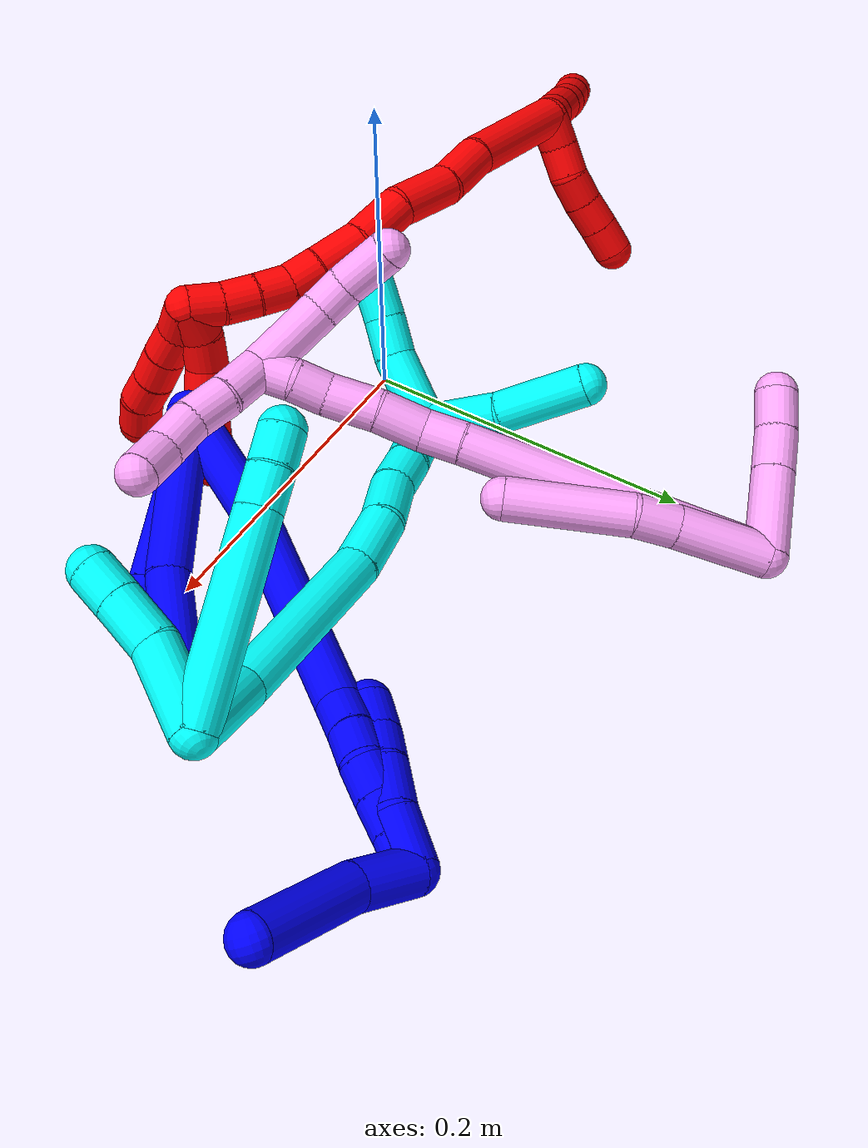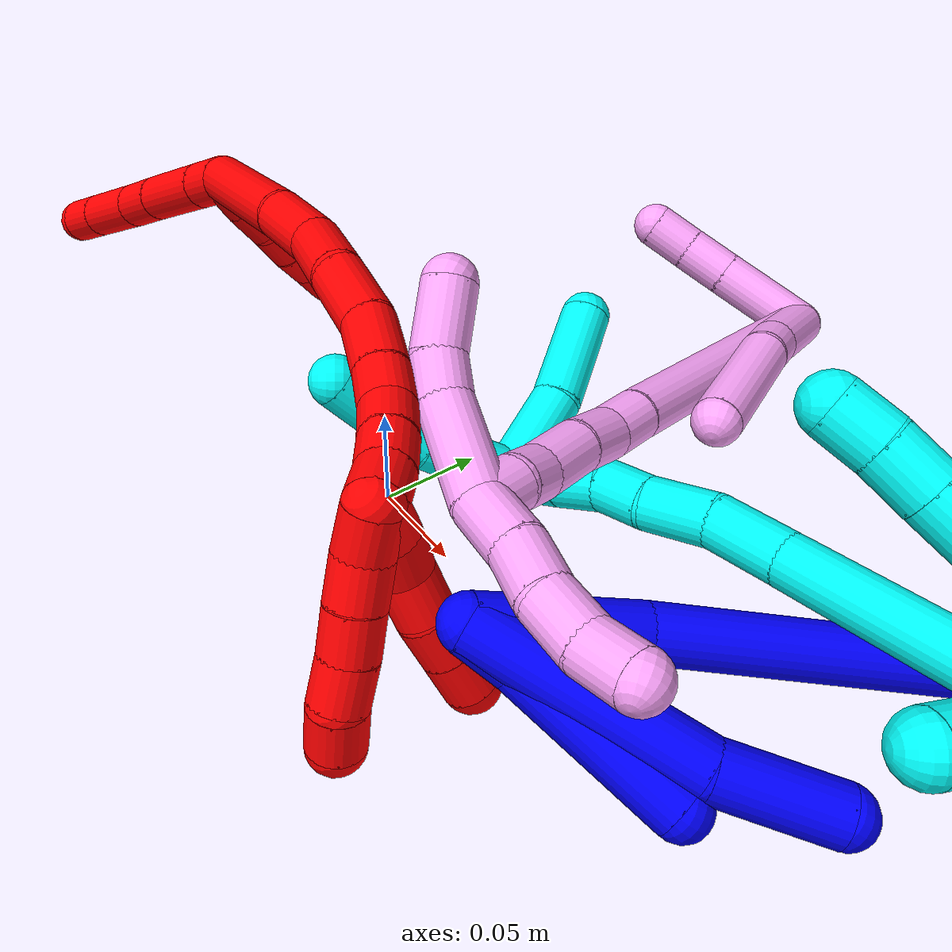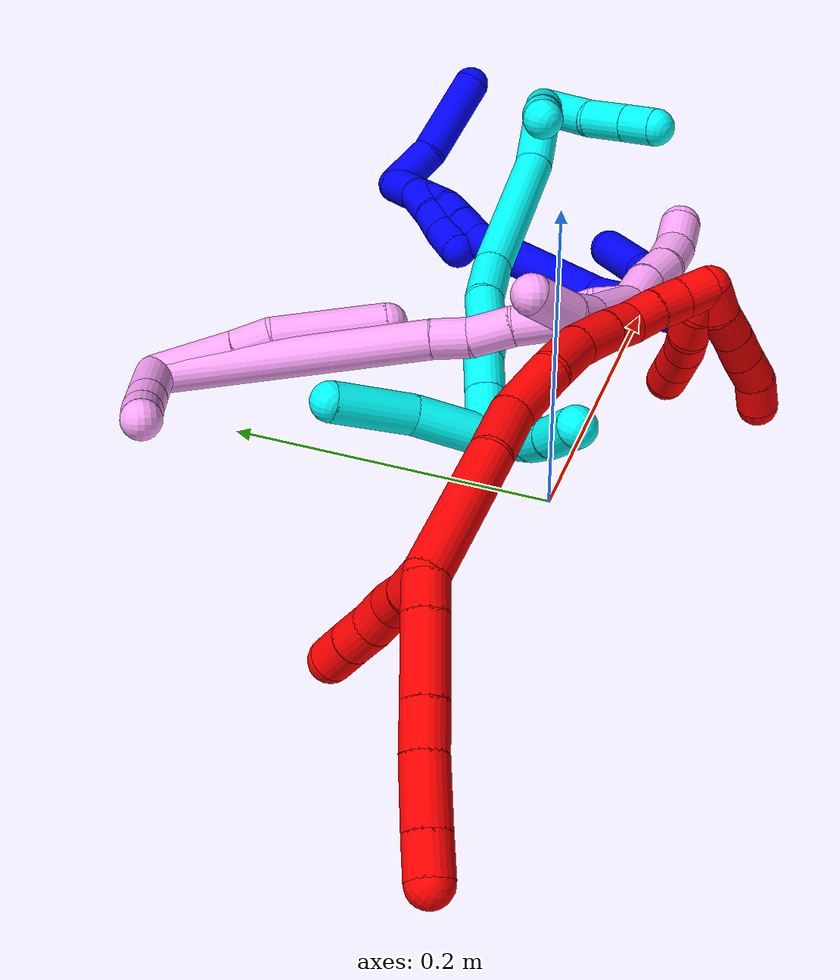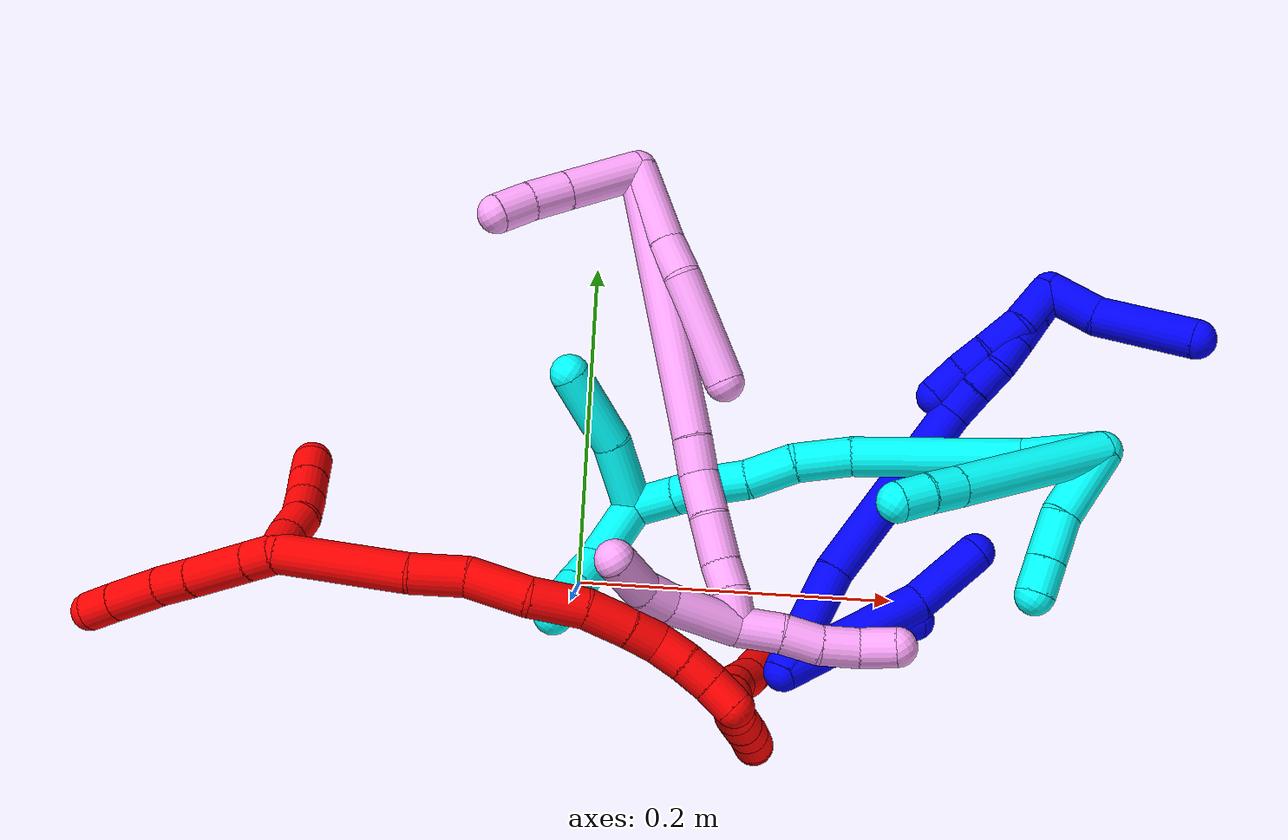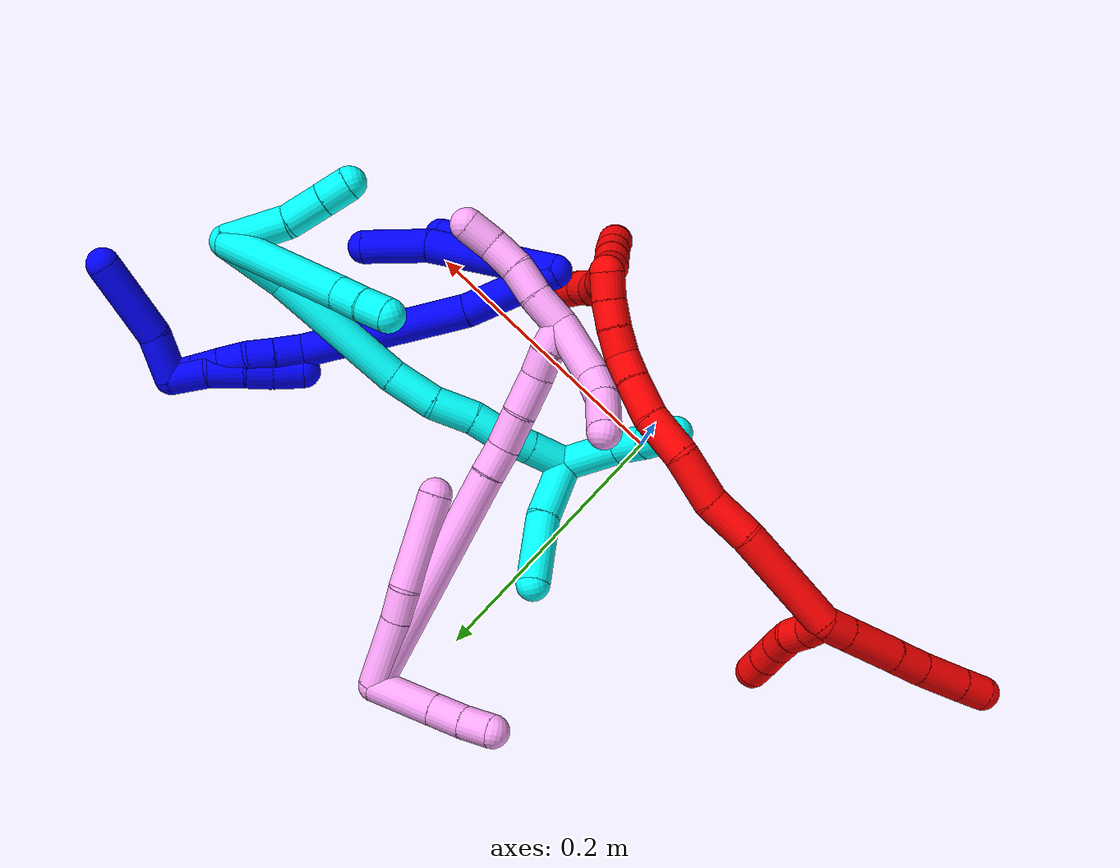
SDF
<sdf version="1.7">
 <world name="default">
  <plugin name="TubeGeneratorPlugin" filename="libtube_generator_plugin.so"/>
  <model name="photoneo_s_sensor">
   <static>1</static>
   <pose>0 0 2 1.57079 1.57079 3.14159</pose>
   <link name="link">
    <inertial><mass>0.1</mass></inertial>
    <sensor name="sensor" type="depth">
     <update_rate>30</update_rate>
     <camera>
      <horizontal_fov>1.22</horizontal_fov>
      <image><width>1920</width><height>1200</height><format>B8G8R8</format></image>
      <clip><near>0.1</near><far>4</far></clip>
      <depth_camera><output>points</output></depth_camera>
     </camera>
     <plugin name="camera_plugin" filename="libgazebo_ros_depth_camera.so">
      <baseline>0.2</baseline>
      <alwaysOn>1</alwaysOn>
      <updateRate>0.0</updateRate>
      <cameraName>camera_ir</cameraName>
      <imageTopicName>/camera/color/image_raw</imageTopicName>
      <cameraInfoTopicName>/camera/color/camera_info</cameraInfoTopicName>
      <depthImageTopicName>/camera/depth/image_raw</depthImageTopicName>
      <depthImageCameraInfoTopicName>/camera/depth/camera_info</depthImageCameraInfoTopicName>
      <pointCloudTopicName>/camera/depth/points</pointCloudTopicName>
      <frameName>fr_optical</frameName>
      <pointCloudCutoff>0.1</pointCloudCutoff>
      <pointCloudCutoffMax>2.0</pointCloudCutoffMax>
      <distortionK1>0</distortionK1>
      <distortionK2>0</distortionK2>
      <distortionK3>0</distortionK3>
      <distortionT1>0</distortionT1>
      <distortionT2>0</distortionT2>
      <CxPrime>0</CxPrime>
      <Cx>0</Cx>
      <Cy>0</Cy>
      <focalLength>0</focalLength>
      <hackBaseline>0</hackBaseline>
     </plugin>
    </sensor>
   </link>
  </model>
  <gravity>0 0 -9.8</gravity>
  <magnetic_field>6e-06 2.3e-05 -4.2e-05</magnetic_field>
  <atmosphere type="adiabatic"/>
  <physics name="default_physics" default="0" type="ode">
   <max_step_size>0.003</max_step_size>
   <real_time_factor>1</real_time_factor>
   <real_time_update_rate>1000</real_time_update_rate>
   <max_contacts>10000</max_contacts>
   <ode>
    <solver>
     <type>quick</type>
     <iters>100</iters>
     <sor>1.3</sor>
     <use_dynamic_moi_rescaling>0</use_dynamic_moi_rescaling>
    </solver>
    <constraints>
     <contact_max_correcting_vel>0</contact_max_correcting_vel>
     <contact_surface_layer>0.001</contact_surface_layer>
     <cfm>0</cfm>
     <erp>0.2</erp>
    </constraints>
   </ode>
  </physics>
  <scene><ambient>0.4 0.4 0.4 1</ambient><background>0.7 0.7 0.7 1</background><shadows>0</shadows></scene>
  <audio><device>default</device></audio>
  <spherical_coordinates>
   <surface_model>EARTH_WGS84</surface_model>
   <latitude_deg>0</latitude_deg>
   <longitude_deg>0</longitude_deg>
   <elevation>0</elevation>
   <heading_deg>0</heading_deg>
  </spherical_coordinates>
  <model name="bin">
   <static>1</static>
   <link name="bottom">
    <collision name="collision-bottom">
     <pose>0 0 -0.01 0 -0 0</pose>
     <geometry><box><size>0.8 0.6 0.02</size></box></geometry>
     <surface>
      <friction><ode><mu>100</mu><mu2>100</mu2></ode></friction>
      <contact><collide_bitmask>65535</collide_bitmask></contact>
     </surface>
    </collision>
   </link>
   <link name="west_wall">
    <collision name="collision-west_wall">
     <pose>-0.41 0 0.1 0 -0 0</pose>
     <geometry><box><size>0.02 0.6 0.2</size></box></geometry>
     <surface>
      <friction><ode><mu>100</mu><mu2>100</mu2></ode></friction>
      <contact><collide_bitmask>65535</collide_bitmask></contact>
     </surface>
    </collision>
   </link>
   <link name="east_wall">
    <collision name="collision-east_wall">
     <pose>0.41 0 0.1 0 -0 0</pose>
     <geometry><box><size>0.02 0.6 0.2</size></box></geometry>
     <surface>
      <friction><ode><mu>100</mu><mu2>100</mu2></ode></friction>
      <contact><collide_bitmask>65535</collide_bitmask></contact>
     </surface>
    </collision>
   </link>
   <link name="south_wall">
    <collision name="collision-south_wall">
     <pose>0 -0.31 0.1 0 -0 0</pose>
     <geometry><box><size>0.8 0.02 0.2</size></box></geometry>
     <surface>
      <friction><ode><mu>100</mu><mu2>100</mu2></ode></friction>
      <contact><collide_bitmask>65535</collide_bitmask></contact>
     </surface>
    </collision>
   </link>
   <link name="north_wall">
    <collision name="collision-north_wall">
     <pose>0 0.31 0.1 0 -0 0</pose>
     <geometry><box><size>0.8 0.02 0.2</size></box></geometry>
     <surface>
      <friction><ode><mu>100</mu><mu2>100</mu2></ode></friction>
      <contact><collide_bitmask>65535</collide_bitmask></contact>
     </surface>
    </collision>
   </link>
  </model>
  <model name="1">
   <static>0</static>
   <link name="1">
    <collision name="collision-cylinder-e_1_2_8">
     <pose>0.005926 0.026639 0.041628 -0.56926 0.119333 -0.034952</pose>
     <geometry><cylinder><radius>0.0125</radius><length>0.099551</length></cylinder></geometry>
     <surface>
      <friction><ode><mu>1.16</mu><mu2>1.16</mu2><slip1>0</slip1><slip2>0</slip2></ode></friction>
      <contact><ode><kp>1e+06</kp><kd>1</kd><max_vel>0</max_vel><min_depth>0.001</min_depth></ode></contact>
     </surface>
    </collision>
    <visual name="visual-cylinder-e_1_2_8">
     <pose>0.005926 0.026639 0.041628 -0.56926 0.119333 -0.034952</pose>
     <geometry><cylinder><radius>0.0125</radius><length>0.099551</length></cylinder></geometry>
     <material><ambient>0 0 1 1</ambient></material>
    </visual>
    <collision name="collision-cylinder-e_2_8_6">
     <pose>0.01939 0.063236 0.105171 -0.426524 0.303489 -0.066207</pose>
     <geometry><cylinder><radius>0.0125</radius><length>0.050449</length></cylinder></geometry>
     <surface>
      <friction><ode><mu>1.16</mu><mu2>1.16</mu2><slip1>0</slip1><slip2>0</slip2></ode></friction>
      <contact><ode><kp>1e+06</kp><kd>1</kd><max_vel>0</max_vel><min_depth>0.001</min_depth></ode></contact>
     </surface>
    </collision>
    <visual name="visual-cylinder-e_2_8_6">
     <pose>0.01939 0.063236 0.105171 -0.426524 0.303489 -0.066207</pose>
     <geometry><cylinder><radius>0.0125</radius><length>0.050449</length></cylinder></geometry>
     <material><ambient>0 0 1 1</ambient></material>
    </visual>
    <collision name="collision-cylinder-e_1_2_9">
     <pose>-0.000375 0.004356 0.010664 -0.387774 -0.03258 0.006398</pose>
     <geometry><cylinder><radius>0.0125</radius><length>0.02305</length></cylinder></geometry>
     <surface>
      <friction><ode><mu>1.16</mu><mu2>1.16</mu2><slip1>0</slip1><slip2>0</slip2></ode></friction>
      <contact><ode><kp>1e+06</kp><kd>1</kd><max_vel>0</max_vel><min_depth>0.001</min_depth></ode></contact>
     </surface>
    </collision>
    <visual name="visual-cylinder-e_1_2_9">
     <pose>-0.000375 0.004356 0.010664 -0.387774 -0.03258 0.006398</pose>
     <geometry><cylinder><radius>0.0125</radius><length>0.02305</length></cylinder></geometry>
     <material><ambient>0 0 1 1</ambient></material>
    </visual>
    <collision name="collision-cylinder-e_2_9_5">
     <pose>-0.003172 0.031211 0.052443 -0.626063 -0.062982 0.020392</pose>
     <geometry><cylinder><radius>0.0125</radius><length>0.07695</length></cylinder></geometry>
     <surface>
      <friction><ode><mu>1.16</mu><mu2>1.16</mu2><slip1>0</slip1><slip2>0</slip2></ode></friction>
      <contact><ode><kp>1e+06</kp><kd>1</kd><max_vel>0</max_vel><min_depth>0.001</min_depth></ode></contact>
     </surface>
    </collision>
    <visual name="visual-cylinder-e_2_9_5">
     <pose>-0.003172 0.031211 0.052443 -0.626063 -0.062982 0.020392</pose>
     <geometry><cylinder><radius>0.0125</radius><length>0.07695</length></cylinder></geometry>
     <material><ambient>0 0 1 1</ambient></material>
    </visual>
    <collision name="collision-cylinder-e_1_2_10">
     <pose>0.016101 0.001353 0.032025 -0.042237 0.465493 -0.010013</pose>
     <geometry><cylinder><radius>0.0125</radius><length>0.07174</length></cylinder></geometry>
     <surface>
      <friction><ode><mu>1.16</mu><mu2>1.16</mu2><slip1>0</slip1><slip2>0</slip2></ode></friction>
      <contact><ode><kp>1e+06</kp><kd>1</kd><max_vel>0</max_vel><min_depth>0.001</min_depth></ode></contact>
     </surface>
    </collision>
    <visual name="visual-cylinder-e_1_2_10">
     <pose>0.016101 0.001353 0.032025 -0.042237 0.465493 -0.010013</pose>
     <geometry><cylinder><radius>0.0125</radius><length>0.07174</length></cylinder></geometry>
     <material><ambient>0 0 1 1</ambient></material>
    </visual>
    <collision name="collision-cylinder-e_2_10_11">
     <pose>0.061383 0.016496 0.118464 -0.248183 0.4794 -0.06095</pose>
     <geometry><cylinder><radius>0.0125</radius><length>0.126531</length></cylinder></geometry>
     <surface>
      <friction><ode><mu>1.16</mu><mu2>1.16</mu2><slip1>0</slip1><slip2>0</slip2></ode></friction>
      <contact><ode><kp>1e+06</kp><kd>1</kd><max_vel>0</max_vel><min_depth>0.001</min_depth></ode></contact>
     </surface>
    </collision>
    <visual name="visual-cylinder-e_2_10_11">
     <pose>0.061383 0.016496 0.118464 -0.248183 0.4794 -0.06095</pose>
     <geometry><cylinder><radius>0.0125</radius><length>0.126531</length></cylinder></geometry>
     <material><ambient>0 0 1 1</ambient></material>
    </visual>
    <collision name="collision-cylinder-e_3_11_12">
     <pose>0.097565 0.034279 0.180044 -0.508527 0.706395 -0.191036</pose>
     <geometry><cylinder><radius>0.0125</radius><length>0.021572</length></cylinder></geometry>
     <surface>
      <friction><ode><mu>1.16</mu><mu2>1.16</mu2><slip1>0</slip1><slip2>0</slip2></ode></friction>
      <contact><ode><kp>1e+06</kp><kd>1</kd><max_vel>0</max_vel><min_depth>0.001</min_depth></ode></contact>
     </surface>
    </collision>
    <visual name="visual-cylinder-e_3_11_12">
     <pose>0.097565 0.034279 0.180044 -0.508527 0.706395 -0.191036</pose>
     <geometry><cylinder><radius>0.0125</radius><length>0.021572</length></cylinder></geometry>
     <material><ambient>0 0 1 1</ambient></material>
    </visual>
    <collision name="collision-cylinder-e_4_12_13">
     <pose>0.110524 0.042136 0.194294 -0.499099 0.636095 -0.167421</pose>
     <geometry><cylinder><radius>0.0125</radius><length>0.020058</length></cylinder></geometry>
     <surface>
      <friction><ode><mu>1.16</mu><mu2>1.16</mu2><slip1>0</slip1><slip2>0</slip2></ode></friction>
      <contact><ode><kp>1e+06</kp><kd>1</kd><max_vel>0</max_vel><min_depth>0.001</min_depth></ode></contact>
     </surface>
    </collision>
    <visual name="visual-cylinder-e_4_12_13">
     <pose>0.110524 0.042136 0.194294 -0.499099 0.636095 -0.167421</pose>
     <geometry><cylinder><radius>0.0125</radius><length>0.020058</length></cylinder></geometry>
     <material><ambient>0 0 1 1</ambient></material>
    </visual>
    <collision name="collision-cylinder-e_5_13_14">
     <pose>0.121071 0.048092 0.210034 -0.23737 0.475856 -0.057823</pose>
     <geometry><cylinder><radius>0.0125</radius><length>0.020039</length></cylinder></geometry>
     <surface>
      <friction><ode><mu>1.16</mu><mu2>1.16</mu2><slip1>0</slip1><slip2>0</slip2></ode></friction>
      <contact><ode><kp>1e+06</kp><kd>1</kd><max_vel>0</max_vel><min_depth>0.001</min_depth></ode></contact>
     </surface>
    </collision>
    <visual name="visual-cylinder-e_5_13_14">
     <pose>0.121071 0.048092 0.210034 -0.23737 0.475856 -0.057823</pose>
     <geometry><cylinder><radius>0.0125</radius><length>0.020039</length></cylinder></geometry>
     <material><ambient>0 0 1 1</ambient></material>
    </visual>
    <collision name="collision-cylinder-e_6_14_15">
     <pose>0.1305 0.052117 0.227238 -0.222231 0.50451 -0.0575</pose>
     <geometry><cylinder><radius>0.0125</radius><length>0.020019</length></cylinder></geometry>
     <surface>
      <friction><ode><mu>1.16</mu><mu2>1.16</mu2><slip1>0</slip1><slip2>0</slip2></ode></friction>
      <contact><ode><kp>1e+06</kp><kd>1</kd><max_vel>0</max_vel><min_depth>0.001</min_depth></ode></contact>
     </surface>
    </collision>
    <visual name="visual-cylinder-e_6_14_15">
     <pose>0.1305 0.052117 0.227238 -0.222231 0.50451 -0.0575</pose>
     <geometry><cylinder><radius>0.0125</radius><length>0.020019</length></cylinder></geometry>
     <material><ambient>0 0 1 1</ambient></material>
    </visual>
    <collision name="collision-cylinder-e_7_15_1">
     <pose>0.140125 0.056092 0.244347 -0.234281 0.498087 -0.059839</pose>
     <geometry><cylinder><radius>0.0125</radius><length>0.020041</length></cylinder></geometry>
     <surface>
      <friction><ode><mu>1.16</mu><mu2>1.16</mu2><slip1>0</slip1><slip2>0</slip2></ode></friction>
      <contact><ode><kp>1e+06</kp><kd>1</kd><max_vel>0</max_vel><min_depth>0.001</min_depth></ode></contact>
     </surface>
    </collision>
    <visual name="visual-cylinder-e_7_15_1">
     <pose>0.140125 0.056092 0.244347 -0.234281 0.498087 -0.059839</pose>
     <geometry><cylinder><radius>0.0125</radius><length>0.020041</length></cylinder></geometry>
     <material><ambient>0 0 1 1</ambient></material>
    </visual>
    <collision name="collision-cylinder-e_1_1_16">
     <pose>0.143988 0.075453 0.249761 -1.75065 -0.052464 0.062856</pose>
     <geometry><cylinder><radius>0.0125</radius><length>0.035252</length></cylinder></geometry>
     <surface>
      <friction><ode><mu>1.16</mu><mu2>1.16</mu2><slip1>0</slip1><slip2>0</slip2></ode></friction>
      <contact><ode><kp>1e+06</kp><kd>1</kd><max_vel>0</max_vel><min_depth>0.001</min_depth></ode></contact>
     </surface>
    </collision>
    <visual name="visual-cylinder-e_1_1_16">
     <pose>0.143988 0.075453 0.249761 -1.75065 -0.052464 0.062856</pose>
     <geometry><cylinder><radius>0.0125</radius><length>0.035252</length></cylinder></geometry>
     <material><ambient>0 0 1 1</ambient></material>
    </visual>
    <collision name="collision-cylinder-e_2_16_4">
     <pose>0.148313 0.124684 0.245166 -1.61608 0.162858 -0.170369</pose>
     <geometry><cylinder><radius>0.0125</radius><length>0.064748</length></cylinder></geometry>
     <surface>
      <friction><ode><mu>1.16</mu><mu2>1.16</mu2><slip1>0</slip1><slip2>0</slip2></ode></friction>
      <contact><ode><kp>1e+06</kp><kd>1</kd><max_vel>0</max_vel><min_depth>0.001</min_depth></ode></contact>
     </surface>
    </collision>
    <visual name="visual-cylinder-e_2_16_4">
     <pose>0.148313 0.124684 0.245166 -1.61608 0.162858 -0.170369</pose>
     <geometry><cylinder><radius>0.0125</radius><length>0.064748</length></cylinder></geometry>
     <material><ambient>0 0 1 1</ambient></material>
    </visual>
    <collision name="collision-cylinder-e_1_1_17">
     <pose>0.139148 0.054354 0.239704 2.86273 -0.397336 -1.92404</pose>
     <geometry><cylinder><radius>0.0125</radius><length>0.029794</length></cylinder></geometry>
     <surface>
      <friction><ode><mu>1.16</mu><mu2>1.16</mu2><slip1>0</slip1><slip2>0</slip2></ode></friction>
      <contact><ode><kp>1e+06</kp><kd>1</kd><max_vel>0</max_vel><min_depth>0.001</min_depth></ode></contact>
     </surface>
    </collision>
    <visual name="visual-cylinder-e_1_1_17">
     <pose>0.139148 0.054354 0.239704 2.86273 -0.397336 -1.92404</pose>
     <geometry><cylinder><radius>0.0125</radius><length>0.029794</length></cylinder></geometry>
     <material><ambient>0 0 1 1</ambient></material>
    </visual>
    <collision name="collision-cylinder-e_2_17_18">
     <pose>0.126891 0.044109 0.21645 2.56996 -0.49775 -1.42609</pose>
     <geometry><cylinder><radius>0.0125</radius><length>0.027196</length></cylinder></geometry>
     <surface>
      <friction><ode><mu>1.16</mu><mu2>1.16</mu2><slip1>0</slip1><slip2>0</slip2></ode></friction>
      <contact><ode><kp>1e+06</kp><kd>1</kd><max_vel>0</max_vel><min_depth>0.001</min_depth></ode></contact>
     </surface>
    </collision>
    <visual name="visual-cylinder-e_2_17_18">
     <pose>0.126891 0.044109 0.21645 2.56996 -0.49775 -1.42609</pose>
     <geometry><cylinder><radius>0.0125</radius><length>0.027196</length></cylinder></geometry>
     <material><ambient>0 0 1 1</ambient></material>
    </visual>
    <collision name="collision-cylinder-e_3_18_19">
     <pose>0.114572 0.032246 0.20008 2.43475 -0.611284 -1.41513</pose>
     <geometry><cylinder><radius>0.0125</radius><length>0.020303</length></cylinder></geometry>
     <surface>
      <friction><ode><mu>1.16</mu><mu2>1.16</mu2><slip1>0</slip1><slip2>0</slip2></ode></friction>
      <contact><ode><kp>1e+06</kp><kd>1</kd><max_vel>0</max_vel><min_depth>0.001</min_depth></ode></contact>
     </surface>
    </collision>
    <visual name="visual-cylinder-e_3_18_19">
     <pose>0.114572 0.032246 0.20008 2.43475 -0.611284 -1.41513</pose>
     <geometry><cylinder><radius>0.0125</radius><length>0.020303</length></cylinder></geometry>
     <material><ambient>0 0 1 1</ambient></material>
    </visual>
    <collision name="collision-cylinder-e_4_19_3">
     <pose>0.102336 0.021791 0.185869 2.57158 -0.599997 -1.62508</pose>
     <geometry><cylinder><radius>0.0125</radius><length>0.022707</length></cylinder></geometry>
     <surface>
      <friction><ode><mu>1.16</mu><mu2>1.16</mu2><slip1>0</slip1><slip2>0</slip2></ode></friction>
      <contact><ode><kp>1e+06</kp><kd>1</kd><max_vel>0</max_vel><min_depth>0.001</min_depth></ode></contact>
     </surface>
    </collision>
    <visual name="visual-cylinder-e_4_19_3">
     <pose>0.102336 0.021791 0.185869 2.57158 -0.599997 -1.62508</pose>
     <geometry><cylinder><radius>0.0125</radius><length>0.022707</length></cylinder></geometry>
     <material><ambient>0 0 1 1</ambient></material>
    </visual>
    <collision name="collision-sphere-3">
     <pose>0.095925 0.016734 0.17798 0 -0 0</pose>
     <geometry><sphere><radius>0.0125</radius></sphere></geometry>
     <surface>
      <friction><ode><mu>1.16</mu><mu2>1.16</mu2><slip1>0</slip1><slip2>0</slip2></ode></friction>
      <contact><ode><kp>1e+06</kp><kd>1</kd><max_vel>0</max_vel><min_depth>0.001</min_depth></ode></contact>
     </surface>
    </collision>
    <visual name="visual-sphere-3">
     <pose>0.095925 0.016734 0.17798 0 -0 0</pose>
     <geometry><sphere><radius>0.0125</radius></sphere></geometry>
     <material><ambient>0 0 1 1</ambient></material>
    </visual>
    <collision name="collision-sphere-19">
     <pose>0.108746 0.026848 0.193758 0 -0 0</pose>
     <geometry><sphere><radius>0.0125</radius></sphere></geometry>
     <surface>
      <friction><ode><mu>1.16</mu><mu2>1.16</mu2><slip1>0</slip1><slip2>0</slip2></ode></friction>
      <contact><ode><kp>1e+06</kp><kd>1</kd><max_vel>0</max_vel><min_depth>0.001</min_depth></ode></contact>
     </surface>
    </collision>
    <visual name="visual-sphere-19">
     <pose>0.108746 0.026848 0.193758 0 -0 0</pose>
     <geometry><sphere><radius>0.0125</radius></sphere></geometry>
     <material><ambient>0 0 1 1</ambient></material>
    </visual>
    <collision name="collision-sphere-10">
     <pose>0.032202 0.002707 0.06405 0 -0 0</pose>
     <geometry><sphere><radius>0.0125</radius></sphere></geometry>
     <surface>
      <friction><ode><mu>1.16</mu><mu2>1.16</mu2><slip1>0</slip1><slip2>0</slip2></ode></friction>
      <contact><ode><kp>1e+06</kp><kd>1</kd><max_vel>0</max_vel><min_depth>0.001</min_depth></ode></contact>
     </surface>
    </collision>
    <visual name="visual-sphere-10">
     <pose>0.032202 0.002707 0.06405 0 -0 0</pose>
     <geometry><sphere><radius>0.0125</radius></sphere></geometry>
     <material><ambient>0 0 1 1</ambient></material>
    </visual>
    <collision name="collision-sphere-5">
     <pose>-0.005594 0.053711 0.083559 0 -0 0</pose>
     <geometry><sphere><radius>0.0125</radius></sphere></geometry>
     <surface>
      <friction><ode><mu>1.16</mu><mu2>1.16</mu2><slip1>0</slip1><slip2>0</slip2></ode></friction>
      <contact><ode><kp>1e+06</kp><kd>1</kd><max_vel>0</max_vel><min_depth>0.001</min_depth></ode></contact>
     </surface>
    </collision>
    <visual name="visual-sphere-5">
     <pose>-0.005594 0.053711 0.083559 0 -0 0</pose>
     <geometry><sphere><radius>0.0125</radius></sphere></geometry>
     <material><ambient>0 0 1 1</ambient></material>
    </visual>
    <collision name="collision-sphere-6">
     <pose>0.026928 0.073195 0.127086 0 -0 0</pose>
     <geometry><sphere><radius>0.0125</radius></sphere></geometry>
     <surface>
      <friction><ode><mu>1.16</mu><mu2>1.16</mu2><slip1>0</slip1><slip2>0</slip2></ode></friction>
      <contact><ode><kp>1e+06</kp><kd>1</kd><max_vel>0</max_vel><min_depth>0.001</min_depth></ode></contact>
     </surface>
    </collision>
    <visual name="visual-sphere-6">
     <pose>0.026928 0.073195 0.127086 0 -0 0</pose>
     <geometry><sphere><radius>0.0125</radius></sphere></geometry>
     <material><ambient>0 0 1 1</ambient></material>
    </visual>
    <collision name="collision-sphere-9">
     <pose>-0.000751 0.008711 0.021327 0 -0 0</pose>
     <geometry><sphere><radius>0.0125</radius></sphere></geometry>
     <surface>
      <friction><ode><mu>1.16</mu><mu2>1.16</mu2><slip1>0</slip1><slip2>0</slip2></ode></friction>
      <contact><ode><kp>1e+06</kp><kd>1</kd><max_vel>0</max_vel><min_depth>0.001</min_depth></ode></contact>
     </surface>
    </collision>
    <visual name="visual-sphere-9">
     <pose>-0.000751 0.008711 0.021327 0 -0 0</pose>
     <geometry><sphere><radius>0.0125</radius></sphere></geometry>
     <material><ambient>0 0 1 1</ambient></material>
    </visual>
    <collision name="collision-sphere-2">
     <geometry><sphere><radius>0.0125</radius></sphere></geometry>
     <surface>
      <friction><ode><mu>1.16</mu><mu2>1.16</mu2><slip1>0</slip1><slip2>0</slip2></ode></friction>
      <contact><ode><kp>1e+06</kp><kd>1</kd><max_vel>0</max_vel><min_depth>0.001</min_depth></ode></contact>
     </surface>
    </collision>
    <visual name="visual-sphere-2">
     <geometry><sphere><radius>0.0125</radius></sphere></geometry>
     <material><ambient>0 0 1 1</ambient></material>
    </visual>
    <collision name="collision-sphere-8">
     <pose>0.011852 0.053277 0.083256 0 -0 0</pose>
     <geometry><sphere><radius>0.0125</radius></sphere></geometry>
     <surface>
      <friction><ode><mu>1.16</mu><mu2>1.16</mu2><slip1>0</slip1><slip2>0</slip2></ode></friction>
      <contact><ode><kp>1e+06</kp><kd>1</kd><max_vel>0</max_vel><min_depth>0.001</min_depth></ode></contact>
     </surface>
    </collision>
    <visual name="visual-sphere-8">
     <pose>0.011852 0.053277 0.083256 0 -0 0</pose>
     <geometry><sphere><radius>0.0125</radius></sphere></geometry>
     <material><ambient>0 0 1 1</ambient></material>
    </visual>
    <collision name="collision-sphere-11">
     <pose>0.090563 0.030285 0.172877 0 -0 0</pose>
     <geometry><sphere><radius>0.0125</radius></sphere></geometry>
     <surface>
      <friction><ode><mu>1.16</mu><mu2>1.16</mu2><slip1>0</slip1><slip2>0</slip2></ode></friction>
      <contact><ode><kp>1e+06</kp><kd>1</kd><max_vel>0</max_vel><min_depth>0.001</min_depth></ode></contact>
     </surface>
    </collision>
    <visual name="visual-sphere-11">
     <pose>0.090563 0.030285 0.172877 0 -0 0</pose>
     <geometry><sphere><radius>0.0125</radius></sphere></geometry>
     <material><ambient>0 0 1 1</ambient></material>
    </visual>
    <collision name="collision-sphere-12">
     <pose>0.104566 0.038274 0.187211 0 -0 0</pose>
     <geometry><sphere><radius>0.0125</radius></sphere></geometry>
     <surface>
      <friction><ode><mu>1.16</mu><mu2>1.16</mu2><slip1>0</slip1><slip2>0</slip2></ode></friction>
      <contact><ode><kp>1e+06</kp><kd>1</kd><max_vel>0</max_vel><min_depth>0.001</min_depth></ode></contact>
     </surface>
    </collision>
    <visual name="visual-sphere-12">
     <pose>0.104566 0.038274 0.187211 0 -0 0</pose>
     <geometry><sphere><radius>0.0125</radius></sphere></geometry>
     <material><ambient>0 0 1 1</ambient></material>
    </visual>
    <collision name="collision-sphere-13">
     <pose>0.116481 0.045997 0.201378 0 -0 0</pose>
     <geometry><sphere><radius>0.0125</radius></sphere></geometry>
     <surface>
      <friction><ode><mu>1.16</mu><mu2>1.16</mu2><slip1>0</slip1><slip2>0</slip2></ode></friction>
      <contact><ode><kp>1e+06</kp><kd>1</kd><max_vel>0</max_vel><min_depth>0.001</min_depth></ode></contact>
     </surface>
    </collision>
    <visual name="visual-sphere-13">
     <pose>0.116481 0.045997 0.201378 0 -0 0</pose>
     <geometry><sphere><radius>0.0125</radius></sphere></geometry>
     <material><ambient>0 0 1 1</ambient></material>
    </visual>
    <collision name="collision-sphere-14">
     <pose>0.125661 0.050186 0.218691 0 -0 0</pose>
     <geometry><sphere><radius>0.0125</radius></sphere></geometry>
     <surface>
      <friction><ode><mu>1.16</mu><mu2>1.16</mu2><slip1>0</slip1><slip2>0</slip2></ode></friction>
      <contact><ode><kp>1e+06</kp><kd>1</kd><max_vel>0</max_vel><min_depth>0.001</min_depth></ode></contact>
     </surface>
    </collision>
    <visual name="visual-sphere-14">
     <pose>0.125661 0.050186 0.218691 0 -0 0</pose>
     <geometry><sphere><radius>0.0125</radius></sphere></geometry>
     <material><ambient>0 0 1 1</ambient></material>
    </visual>
    <collision name="collision-sphere-15">
     <pose>0.135338 0.054048 0.235784 0 -0 0</pose>
     <geometry><sphere><radius>0.0125</radius></sphere></geometry>
     <surface>
      <friction><ode><mu>1.16</mu><mu2>1.16</mu2><slip1>0</slip1><slip2>0</slip2></ode></friction>
      <contact><ode><kp>1e+06</kp><kd>1</kd><max_vel>0</max_vel><min_depth>0.001</min_depth></ode></contact>
     </surface>
    </collision>
    <visual name="visual-sphere-15">
     <pose>0.135338 0.054048 0.235784 0 -0 0</pose>
     <geometry><sphere><radius>0.0125</radius></sphere></geometry>
     <material><ambient>0 0 1 1</ambient></material>
    </visual>
    <collision name="collision-sphere-1">
     <pose>0.144913 0.058136 0.25291 0 -0 0</pose>
     <geometry><sphere><radius>0.0125</radius></sphere></geometry>
     <surface>
      <friction><ode><mu>1.16</mu><mu2>1.16</mu2><slip1>0</slip1><slip2>0</slip2></ode></friction>
      <contact><ode><kp>1e+06</kp><kd>1</kd><max_vel>0</max_vel><min_depth>0.001</min_depth></ode></contact>
     </surface>
    </collision>
    <visual name="visual-sphere-1">
     <pose>0.144913 0.058136 0.25291 0 -0 0</pose>
     <geometry><sphere><radius>0.0125</radius></sphere></geometry>
     <material><ambient>0 0 1 1</ambient></material>
    </visual>
    <collision name="collision-sphere-18">
     <pose>0.120399 0.037645 0.206401 0 -0 0</pose>
     <geometry><sphere><radius>0.0125</radius></sphere></geometry>
     <surface>
      <friction><ode><mu>1.16</mu><mu2>1.16</mu2><slip1>0</slip1><slip2>0</slip2></ode></friction>
      <contact><ode><kp>1e+06</kp><kd>1</kd><max_vel>0</max_vel><min_depth>0.001</min_depth></ode></contact>
     </surface>
    </collision>
    <visual name="visual-sphere-18">
     <pose>0.120399 0.037645 0.206401 0 -0 0</pose>
     <geometry><sphere><radius>0.0125</radius></sphere></geometry>
     <material><ambient>0 0 1 1</ambient></material>
    </visual>
    <collision name="collision-sphere-16">
     <pose>0.143064 0.092771 0.246612 0 -0 0</pose>
     <geometry><sphere><radius>0.0125</radius></sphere></geometry>
     <surface>
      <friction><ode><mu>1.16</mu><mu2>1.16</mu2><slip1>0</slip1><slip2>0</slip2></ode></friction>
      <contact><ode><kp>1e+06</kp><kd>1</kd><max_vel>0</max_vel><min_depth>0.001</min_depth></ode></contact>
     </surface>
    </collision>
    <visual name="visual-sphere-16">
     <pose>0.143064 0.092771 0.246612 0 -0 0</pose>
     <geometry><sphere><radius>0.0125</radius></sphere></geometry>
     <material><ambient>0 0 1 1</ambient></material>
    </visual>
    <collision name="collision-sphere-4">
     <pose>0.153562 0.156597 0.24372 0 -0 0</pose>
     <geometry><sphere><radius>0.0125</radius></sphere></geometry>
     <surface>
      <friction><ode><mu>1.16</mu><mu2>1.16</mu2><slip1>0</slip1><slip2>0</slip2></ode></friction>
      <contact><ode><kp>1e+06</kp><kd>1</kd><max_vel>0</max_vel><min_depth>0.001</min_depth></ode></contact>
     </surface>
    </collision>
    <visual name="visual-sphere-4">
     <pose>0.153562 0.156597 0.24372 0 -0 0</pose>
     <geometry><sphere><radius>0.0125</radius></sphere></geometry>
     <material><ambient>0 0 1 1</ambient></material>
    </visual>
    <collision name="collision-sphere-17">
     <pose>0.133383 0.050573 0.226498 0 -0 0</pose>
     <geometry><sphere><radius>0.0125</radius></sphere></geometry>
     <surface>
      <friction><ode><mu>1.16</mu><mu2>1.16</mu2><slip1>0</slip1><slip2>0</slip2></ode></friction>
      <contact><ode><kp>1e+06</kp><kd>1</kd><max_vel>0</max_vel><min_depth>0.001</min_depth></ode></contact>
     </surface>
    </collision>
    <visual name="visual-sphere-17">
     <pose>0.133383 0.050573 0.226498 0 -0 0</pose>
     <geometry><sphere><radius>0.0125</radius></sphere></geometry>
     <material><ambient>0 0 1 1</ambient></material>
    </visual>
    <inertial>
     <pose>0.065775 0.039928 0.131258 0 -0 0</pose>
     <mass>0.75</mass>
     <inertia>
      <ixx>0.000344</ixx>
      <ixy>0</ixy>
      <ixz>0</ixz>
      <iyy>0.000325</iyy>
      <iyz>0</iyz>
      <izz>-0.000223</izz>
     </inertia>
    </inertial>
   </link>
   <pose>0.13029 -0.044235 0.057343 2.6939 -0.765397 1.59016</pose>
  </model>
  <model name="2">
   <static>0</static>
   <link name="2">
    <collision name="collision-cylinder-e_1_2_8">
     <pose>-0.008926 -0.004605 -0.001841 1.95113 -1.06363 -1.43069</pose>
     <geometry><cylinder><radius>0.0125</radius><length>0.020423</length></cylinder></geometry>
     <surface>
      <friction><ode><mu>1.16</mu><mu2>1.16</mu2><slip1>0</slip1><slip2>0</slip2></ode></friction>
      <contact><ode><kp>1e+06</kp><kd>1</kd><max_vel>0</max_vel><min_depth>0.001</min_depth></ode></contact>
     </surface>
    </collision>
    <visual name="visual-cylinder-e_1_2_8">
     <pose>-0.008926 -0.004605 -0.001841 1.95113 -1.06363 -1.43069</pose>
     <geometry><cylinder><radius>0.0125</radius><length>0.020423</length></cylinder></geometry>
     <material><ambient>1 0 0 1</ambient></material>
    </visual>
    <collision name="collision-cylinder-e_2_8_9">
     <pose>-0.037016 -0.019109 -0.007658 1.95272 -1.0629 -1.43156</pose>
     <geometry><cylinder><radius>0.0125</radius><length>0.043865</length></cylinder></geometry>
     <surface>
      <friction><ode><mu>1.16</mu><mu2>1.16</mu2><slip1>0</slip1><slip2>0</slip2></ode></friction>
      <contact><ode><kp>1e+06</kp><kd>1</kd><max_vel>0</max_vel><min_depth>0.001</min_depth></ode></contact>
     </surface>
    </collision>
    <visual name="visual-cylinder-e_2_8_9">
     <pose>-0.037016 -0.019109 -0.007658 1.95272 -1.0629 -1.43156</pose>
     <geometry><cylinder><radius>0.0125</radius><length>0.043865</length></cylinder></geometry>
     <material><ambient>1 0 0 1</ambient></material>
    </visual>
    <collision name="collision-cylinder-e_3_9_10">
     <pose>-0.067494 -0.034797 -0.014259 1.99655 -1.05882 -1.47424</pose>
     <geometry><cylinder><radius>0.0125</radius><length>0.025956</length></cylinder></geometry>
     <surface>
      <friction><ode><mu>1.16</mu><mu2>1.16</mu2><slip1>0</slip1><slip2>0</slip2></ode></friction>
      <contact><ode><kp>1e+06</kp><kd>1</kd><max_vel>0</max_vel><min_depth>0.001</min_depth></ode></contact>
     </surface>
    </collision>
    <visual name="visual-cylinder-e_3_9_10">
     <pose>-0.067494 -0.034797 -0.014259 1.99655 -1.05882 -1.47424</pose>
     <geometry><cylinder><radius>0.0125</radius><length>0.025956</length></cylinder></geometry>
     <material><ambient>1 0 0 1</ambient></material>
    </visual>
    <collision name="collision-cylinder-e_4_10_11">
     <pose>-0.094873 -0.049546 -0.019755 1.88085 -1.04104 -1.33182</pose>
     <geometry><cylinder><radius>0.0125</radius><length>0.037234</length></cylinder></geometry>
     <surface>
      <friction><ode><mu>1.16</mu><mu2>1.16</mu2><slip1>0</slip1><slip2>0</slip2></ode></friction>
      <contact><ode><kp>1e+06</kp><kd>1</kd><max_vel>0</max_vel><min_depth>0.001</min_depth></ode></contact>
     </surface>
    </collision>
    <visual name="visual-cylinder-e_4_10_11">
     <pose>-0.094873 -0.049546 -0.019755 1.88085 -1.04104 -1.33182</pose>
     <geometry><cylinder><radius>0.0125</radius><length>0.037234</length></cylinder></geometry>
     <material><ambient>1 0 0 1</ambient></material>
    </visual>
    <collision name="collision-cylinder-e_5_11_6">
     <pose>-0.120582 -0.064077 -0.024288 1.86073 -1.02827 -1.29708</pose>
     <geometry><cylinder><radius>0.0125</radius><length>0.022523</length></cylinder></geometry>
     <surface>
      <friction><ode><mu>1.16</mu><mu2>1.16</mu2><slip1>0</slip1><slip2>0</slip2></ode></friction>
      <contact><ode><kp>1e+06</kp><kd>1</kd><max_vel>0</max_vel><min_depth>0.001</min_depth></ode></contact>
     </surface>
    </collision>
    <visual name="visual-cylinder-e_5_11_6">
     <pose>-0.120582 -0.064077 -0.024288 1.86073 -1.02827 -1.29708</pose>
     <geometry><cylinder><radius>0.0125</radius><length>0.022523</length></cylinder></geometry>
     <material><ambient>1 0 0 1</ambient></material>
    </visual>
    <collision name="collision-cylinder-e_1_2_12">
     <pose>0.000264 0.000131 -0.009996 -3.12846 0.026414 -2.21886</pose>
     <geometry><cylinder><radius>0.0125</radius><length>0.02</length></cylinder></geometry>
     <surface>
      <friction><ode><mu>1.16</mu><mu2>1.16</mu2><slip1>0</slip1><slip2>0</slip2></ode></friction>
      <contact><ode><kp>1e+06</kp><kd>1</kd><max_vel>0</max_vel><min_depth>0.001</min_depth></ode></contact>
     </surface>
    </collision>
    <visual name="visual-cylinder-e_1_2_12">
     <pose>0.000264 0.000131 -0.009996 -3.12846 0.026414 -2.21886</pose>
     <geometry><cylinder><radius>0.0125</radius><length>0.02</length></cylinder></geometry>
     <material><ambient>1 0 0 1</ambient></material>
    </visual>
    <collision name="collision-cylinder-e_2_12_13">
     <pose>0.002452 0.001346 -0.029744 -3.03091 0.193622 -2.10479</pose>
     <geometry><cylinder><radius>0.0125</radius><length>0.02</length></cylinder></geometry>
     <surface>
      <friction><ode><mu>1.16</mu><mu2>1.16</mu2><slip1>0</slip1><slip2>0</slip2></ode></friction>
      <contact><ode><kp>1e+06</kp><kd>1</kd><max_vel>0</max_vel><min_depth>0.001</min_depth></ode></contact>
     </surface>
    </collision>
    <visual name="visual-cylinder-e_2_12_13">
     <pose>0.002452 0.001346 -0.029744 -3.03091 0.193622 -2.10479</pose>
     <geometry><cylinder><radius>0.0125</radius><length>0.02</length></cylinder></geometry>
     <material><ambient>1 0 0 1</ambient></material>
    </visual>
    <collision name="collision-cylinder-e_3_13_14">
     <pose>0.0034 0.003145 -0.049424 -3.0697 -0.097849 1.87464</pose>
     <geometry><cylinder><radius>0.0125</radius><length>0.02</length></cylinder></geometry>
     <surface>
      <friction><ode><mu>1.16</mu><mu2>1.16</mu2><slip1>0</slip1><slip2>0</slip2></ode></friction>
      <contact><ode><kp>1e+06</kp><kd>1</kd><max_vel>0</max_vel><min_depth>0.001</min_depth></ode></contact>
     </surface>
    </collision>
    <visual name="visual-cylinder-e_3_13_14">
     <pose>0.0034 0.003145 -0.049424 -3.0697 -0.097849 1.87464</pose>
     <geometry><cylinder><radius>0.0125</radius><length>0.02</length></cylinder></geometry>
     <material><ambient>1 0 0 1</ambient></material>
    </visual>
    <collision name="collision-cylinder-e_4_14_15">
     <pose>0.001185 0.005516 -0.069134 -2.97393 -0.124057 1.27301</pose>
     <geometry><cylinder><radius>0.0125</radius><length>0.02</length></cylinder></geometry>
     <surface>
      <friction><ode><mu>1.16</mu><mu2>1.16</mu2><slip1>0</slip1><slip2>0</slip2></ode></friction>
      <contact><ode><kp>1e+06</kp><kd>1</kd><max_vel>0</max_vel><min_depth>0.001</min_depth></ode></contact>
     </surface>
    </collision>
    <visual name="visual-cylinder-e_4_14_15">
     <pose>0.001185 0.005516 -0.069134 -2.97393 -0.124057 1.27301</pose>
     <geometry><cylinder><radius>0.0125</radius><length>0.02</length></cylinder></geometry>
     <material><ambient>1 0 0 1</ambient></material>
    </visual>
    <collision name="collision-cylinder-e_5_15_5">
     <pose>-0.001111 0.008609 -0.088758 -2.99653 -0.106039 1.26168</pose>
     <geometry><cylinder><radius>0.0125</radius><length>0.02</length></cylinder></geometry>
     <surface>
      <friction><ode><mu>1.16</mu><mu2>1.16</mu2><slip1>0</slip1><slip2>0</slip2></ode></friction>
      <contact><ode><kp>1e+06</kp><kd>1</kd><max_vel>0</max_vel><min_depth>0.001</min_depth></ode></contact>
     </surface>
    </collision>
    <visual name="visual-cylinder-e_5_15_5">
     <pose>-0.001111 0.008609 -0.088758 -2.99653 -0.106039 1.26168</pose>
     <geometry><cylinder><radius>0.0125</radius><length>0.02</length></cylinder></geometry>
     <material><ambient>1 0 0 1</ambient></material>
    </visual>
    <collision name="collision-cylinder-e_1_2_16">
     <pose>0.041167 -0.000145 0.005015 0.028958 1.44952 0.025643</pose>
     <geometry><cylinder><radius>0.0125</radius><length>0.082943</length></cylinder></geometry>
     <surface>
      <friction><ode><mu>1.16</mu><mu2>1.16</mu2><slip1>0</slip1><slip2>0</slip2></ode></friction>
      <contact><ode><kp>1e+06</kp><kd>1</kd><max_vel>0</max_vel><min_depth>0.001</min_depth></ode></contact>
     </surface>
    </collision>
    <visual name="visual-cylinder-e_1_2_16">
     <pose>0.041167 -0.000145 0.005015 0.028958 1.44952 0.025643</pose>
     <geometry><cylinder><radius>0.0125</radius><length>0.082943</length></cylinder></geometry>
     <material><ambient>1 0 0 1</ambient></material>
    </visual>
    <collision name="collision-cylinder-e_2_16_17">
     <pose>0.099672 -0.000479 0.008884 2.97876 1.50391 2.96754</pose>
     <geometry><cylinder><radius>0.0125</radius><length>0.034755</length></cylinder></geometry>
     <surface>
      <friction><ode><mu>1.16</mu><mu2>1.16</mu2><slip1>0</slip1><slip2>0</slip2></ode></friction>
      <contact><ode><kp>1e+06</kp><kd>1</kd><max_vel>0</max_vel><min_depth>0.001</min_depth></ode></contact>
     </surface>
    </collision>
    <visual name="visual-cylinder-e_2_16_17">
     <pose>0.099672 -0.000479 0.008884 2.97876 1.50391 2.96754</pose>
     <geometry><cylinder><radius>0.0125</radius><length>0.034755</length></cylinder></geometry>
     <material><ambient>1 0 0 1</ambient></material>
    </visual>
    <collision name="collision-cylinder-e_3_17_18">
     <pose>0.135819 -0.004458 0.010112 1.01135 1.3373 0.824745</pose>
     <geometry><cylinder><radius>0.0125</radius><length>0.038665</length></cylinder></geometry>
     <surface>
      <friction><ode><mu>1.16</mu><mu2>1.16</mu2><slip1>0</slip1><slip2>0</slip2></ode></friction>
      <contact><ode><kp>1e+06</kp><kd>1</kd><max_vel>0</max_vel><min_depth>0.001</min_depth></ode></contact>
     </surface>
    </collision>
    <visual name="visual-cylinder-e_3_17_18">
     <pose>0.135819 -0.004458 0.010112 1.01135 1.3373 0.824745</pose>
     <geometry><cylinder><radius>0.0125</radius><length>0.038665</length></cylinder></geometry>
     <material><ambient>1 0 0 1</ambient></material>
    </visual>
    <collision name="collision-cylinder-e_4_18_19">
     <pose>0.171279 -0.01207 0.010017 2.14453 1.30414 1.90272</pose>
     <geometry><cylinder><radius>0.0125</radius><length>0.034525</length></cylinder></geometry>
     <surface>
      <friction><ode><mu>1.16</mu><mu2>1.16</mu2><slip1>0</slip1><slip2>0</slip2></ode></friction>
      <contact><ode><kp>1e+06</kp><kd>1</kd><max_vel>0</max_vel><min_depth>0.001</min_depth></ode></contact>
     </surface>
    </collision>
    <visual name="visual-cylinder-e_4_18_19">
     <pose>0.171279 -0.01207 0.010017 2.14453 1.30414 1.90272</pose>
     <geometry><cylinder><radius>0.0125</radius><length>0.034525</length></cylinder></geometry>
     <material><ambient>1 0 0 1</ambient></material>
    </visual>
    <collision name="collision-cylinder-e_5_19_20">
     <pose>0.201065 -0.02202 0.006668 1.71337 1.13024 1.26328</pose>
     <geometry><cylinder><radius>0.0125</radius><length>0.029041</length></cylinder></geometry>
     <surface>
      <friction><ode><mu>1.16</mu><mu2>1.16</mu2><slip1>0</slip1><slip2>0</slip2></ode></friction>
      <contact><ode><kp>1e+06</kp><kd>1</kd><max_vel>0</max_vel><min_depth>0.001</min_depth></ode></contact>
     </surface>
    </collision>
    <visual name="visual-cylinder-e_5_19_20">
     <pose>0.201065 -0.02202 0.006668 1.71337 1.13024 1.26328</pose>
     <geometry><cylinder><radius>0.0125</radius><length>0.029041</length></cylinder></geometry>
     <material><ambient>1 0 0 1</ambient></material>
    </visual>
    <collision name="collision-cylinder-e_6_20_21">
     <pose>0.222874 -0.033078 0.00503 1.72357 1.04904 1.18678</pose>
     <geometry><cylinder><radius>0.0125</radius><length>0.020012</length></cylinder></geometry>
     <surface>
      <friction><ode><mu>1.16</mu><mu2>1.16</mu2><slip1>0</slip1><slip2>0</slip2></ode></friction>
      <contact><ode><kp>1e+06</kp><kd>1</kd><max_vel>0</max_vel><min_depth>0.001</min_depth></ode></contact>
     </surface>
    </collision>
    <visual name="visual-cylinder-e_6_20_21">
     <pose>0.222874 -0.033078 0.00503 1.72357 1.04904 1.18678</pose>
     <geometry><cylinder><radius>0.0125</radius><length>0.020012</length></cylinder></geometry>
     <material><ambient>1 0 0 1</ambient></material>
    </visual>
    <collision name="collision-cylinder-e_7_21_22">
     <pose>0.240189 -0.042652 0.006302 1.15858 1.04017 0.716869</pose>
     <geometry><cylinder><radius>0.0125</radius><length>0.020037</length></cylinder></geometry>
     <surface>
      <friction><ode><mu>1.16</mu><mu2>1.16</mu2><slip1>0</slip1><slip2>0</slip2></ode></friction>
      <contact><ode><kp>1e+06</kp><kd>1</kd><max_vel>0</max_vel><min_depth>0.001</min_depth></ode></contact>
     </surface>
    </collision>
    <visual name="visual-cylinder-e_7_21_22">
     <pose>0.240189 -0.042652 0.006302 1.15858 1.04017 0.716869</pose>
     <geometry><cylinder><radius>0.0125</radius><length>0.020037</length></cylinder></geometry>
     <material><ambient>1 0 0 1</ambient></material>
    </visual>
    <collision name="collision-cylinder-e_8_22_23">
     <pose>0.256984 -0.052681 0.010485 1.19049 0.952779 0.672361</pose>
     <geometry><cylinder><radius>0.0125</radius><length>0.02001</length></cylinder></geometry>
     <surface>
      <friction><ode><mu>1.16</mu><mu2>1.16</mu2><slip1>0</slip1><slip2>0</slip2></ode></friction>
      <contact><ode><kp>1e+06</kp><kd>1</kd><max_vel>0</max_vel><min_depth>0.001</min_depth></ode></contact>
     </surface>
    </collision>
    <visual name="visual-cylinder-e_8_22_23">
     <pose>0.256984 -0.052681 0.010485 1.19049 0.952779 0.672361</pose>
     <geometry><cylinder><radius>0.0125</radius><length>0.02001</length></cylinder></geometry>
     <material><ambient>1 0 0 1</ambient></material>
    </visual>
    <collision name="collision-cylinder-e_9_23_1">
     <pose>0.272648 -0.063692 0.016108 1.01829 0.848866 0.49422</pose>
     <geometry><cylinder><radius>0.0125</radius><length>0.020013</length></cylinder></geometry>
     <surface>
      <friction><ode><mu>1.16</mu><mu2>1.16</mu2><slip1>0</slip1><slip2>0</slip2></ode></friction>
      <contact><ode><kp>1e+06</kp><kd>1</kd><max_vel>0</max_vel><min_depth>0.001</min_depth></ode></contact>
     </surface>
    </collision>
    <visual name="visual-cylinder-e_9_23_1">
     <pose>0.272648 -0.063692 0.016108 1.01829 0.848866 0.49422</pose>
     <geometry><cylinder><radius>0.0125</radius><length>0.020013</length></cylinder></geometry>
     <material><ambient>1 0 0 1</ambient></material>
    </visual>
    <collision name="collision-cylinder-e_1_1_24">
     <pose>0.28016 -0.076697 0.012826 2.31204 0.000125 0.000283</pose>
     <geometry><cylinder><radius>0.0125</radius><length>0.02</length></cylinder></geometry>
     <surface>
      <friction><ode><mu>1.16</mu><mu2>1.16</mu2><slip1>0</slip1><slip2>0</slip2></ode></friction>
      <contact><ode><kp>1e+06</kp><kd>1</kd><max_vel>0</max_vel><min_depth>0.001</min_depth></ode></contact>
     </surface>
    </collision>
    <visual name="visual-cylinder-e_1_1_24">
     <pose>0.28016 -0.076697 0.012826 2.31204 0.000125 0.000283</pose>
     <geometry><cylinder><radius>0.0125</radius><length>0.02</length></cylinder></geometry>
     <material><ambient>1 0 0 1</ambient></material>
    </visual>
    <collision name="collision-cylinder-e_2_24_25">
     <pose>0.282217 -0.091766 2.4e-05 2.2372 0.207019 0.421353</pose>
     <geometry><cylinder><radius>0.0125</radius><length>0.02</length></cylinder></geometry>
     <surface>
      <friction><ode><mu>1.16</mu><mu2>1.16</mu2><slip1>0</slip1><slip2>0</slip2></ode></friction>
      <contact><ode><kp>1e+06</kp><kd>1</kd><max_vel>0</max_vel><min_depth>0.001</min_depth></ode></contact>
     </surface>
    </collision>
    <visual name="visual-cylinder-e_2_24_25">
     <pose>0.282217 -0.091766 2.4e-05 2.2372 0.207019 0.421353</pose>
     <geometry><cylinder><radius>0.0125</radius><length>0.02</length></cylinder></geometry>
     <material><ambient>1 0 0 1</ambient></material>
    </visual>
    <collision name="collision-cylinder-e_3_25_26">
     <pose>0.286005 -0.106853 -0.012531 2.29233 0.174163 0.381481</pose>
     <geometry><cylinder><radius>0.0125</radius><length>0.02</length></cylinder></geometry>
     <surface>
      <friction><ode><mu>1.16</mu><mu2>1.16</mu2><slip1>0</slip1><slip2>0</slip2></ode></friction>
      <contact><ode><kp>1e+06</kp><kd>1</kd><max_vel>0</max_vel><min_depth>0.001</min_depth></ode></contact>
     </surface>
    </collision>
    <visual name="visual-cylinder-e_3_25_26">
     <pose>0.286005 -0.106853 -0.012531 2.29233 0.174163 0.381481</pose>
     <geometry><cylinder><radius>0.0125</radius><length>0.02</length></cylinder></geometry>
     <material><ambient>1 0 0 1</ambient></material>
    </visual>
    <collision name="collision-cylinder-e_4_26_27">
     <pose>0.28924 -0.122149 -0.024979 2.21561 0.150779 0.30035</pose>
     <geometry><cylinder><radius>0.0125</radius><length>0.02</length></cylinder></geometry>
     <surface>
      <friction><ode><mu>1.16</mu><mu2>1.16</mu2><slip1>0</slip1><slip2>0</slip2></ode></friction>
      <contact><ode><kp>1e+06</kp><kd>1</kd><max_vel>0</max_vel><min_depth>0.001</min_depth></ode></contact>
     </surface>
    </collision>
    <visual name="visual-cylinder-e_4_26_27">
     <pose>0.28924 -0.122149 -0.024979 2.21561 0.150779 0.30035</pose>
     <geometry><cylinder><radius>0.0125</radius><length>0.02</length></cylinder></geometry>
     <material><ambient>1 0 0 1</ambient></material>
    </visual>
    <collision name="collision-cylinder-e_5_27_4">
     <pose>0.290597 -0.136076 -0.0389 2.4948 -0.01448 -0.043196</pose>
     <geometry><cylinder><radius>0.0125</radius><length>0.02</length></cylinder></geometry>
     <surface>
      <friction><ode><mu>1.16</mu><mu2>1.16</mu2><slip1>0</slip1><slip2>0</slip2></ode></friction>
      <contact><ode><kp>1e+06</kp><kd>1</kd><max_vel>0</max_vel><min_depth>0.001</min_depth></ode></contact>
     </surface>
    </collision>
    <visual name="visual-cylinder-e_5_27_4">
     <pose>0.290597 -0.136076 -0.0389 2.4948 -0.01448 -0.043196</pose>
     <geometry><cylinder><radius>0.0125</radius><length>0.02</length></cylinder></geometry>
     <material><ambient>1 0 0 1</ambient></material>
    </visual>
    <collision name="collision-cylinder-e_1_1_28">
     <pose>0.278334 -0.070847 0.009865 2.98575 -0.183477 -1.73412</pose>
     <geometry><cylinder><radius>0.0125</radius><length>0.02</length></cylinder></geometry>
     <surface>
      <friction><ode><mu>1.16</mu><mu2>1.16</mu2><slip1>0</slip1><slip2>0</slip2></ode></friction>
      <contact><ode><kp>1e+06</kp><kd>1</kd><max_vel>0</max_vel><min_depth>0.001</min_depth></ode></contact>
     </surface>
    </collision>
    <visual name="visual-cylinder-e_1_1_28">
     <pose>0.278334 -0.070847 0.009865 2.98575 -0.183477 -1.73412</pose>
     <geometry><cylinder><radius>0.0125</radius><length>0.02</length></cylinder></geometry>
     <material><ambient>1 0 0 1</ambient></material>
    </visual>
    <collision name="collision-cylinder-e_2_28_29">
     <pose>0.277161 -0.075301 -0.009387 2.84379 0.065192 0.42808</pose>
     <geometry><cylinder><radius>0.0125</radius><length>0.02</length></cylinder></geometry>
     <surface>
      <friction><ode><mu>1.16</mu><mu2>1.16</mu2><slip1>0</slip1><slip2>0</slip2></ode></friction>
      <contact><ode><kp>1e+06</kp><kd>1</kd><max_vel>0</max_vel><min_depth>0.001</min_depth></ode></contact>
     </surface>
    </collision>
    <visual name="visual-cylinder-e_2_28_29">
     <pose>0.277161 -0.075301 -0.009387 2.84379 0.065192 0.42808</pose>
     <geometry><cylinder><radius>0.0125</radius><length>0.02</length></cylinder></geometry>
     <material><ambient>1 0 0 1</ambient></material>
    </visual>
    <collision name="collision-cylinder-e_3_29_30">
     <pose>0.281309 -0.081031 -0.027867 2.83783 0.357152 1.73495</pose>
     <geometry><cylinder><radius>0.0125</radius><length>0.02</length></cylinder></geometry>
     <surface>
      <friction><ode><mu>1.16</mu><mu2>1.16</mu2><slip1>0</slip1><slip2>0</slip2></ode></friction>
      <contact><ode><kp>1e+06</kp><kd>1</kd><max_vel>0</max_vel><min_depth>0.001</min_depth></ode></contact>
     </surface>
    </collision>
    <visual name="visual-cylinder-e_3_29_30">
     <pose>0.281309 -0.081031 -0.027867 2.83783 0.357152 1.73495</pose>
     <geometry><cylinder><radius>0.0125</radius><length>0.02</length></cylinder></geometry>
     <material><ambient>1 0 0 1</ambient></material>
    </visual>
    <collision name="collision-cylinder-e_4_30_31">
     <pose>0.287546 -0.085424 -0.046292 2.97544 0.277696 2.06689</pose>
     <geometry><cylinder><radius>0.0125</radius><length>0.02</length></cylinder></geometry>
     <surface>
      <friction><ode><mu>1.16</mu><mu2>1.16</mu2><slip1>0</slip1><slip2>0</slip2></ode></friction>
      <contact><ode><kp>1e+06</kp><kd>1</kd><max_vel>0</max_vel><min_depth>0.001</min_depth></ode></contact>
     </surface>
    </collision>
    <visual name="visual-cylinder-e_4_30_31">
     <pose>0.287546 -0.085424 -0.046292 2.97544 0.277696 2.06689</pose>
     <geometry><cylinder><radius>0.0125</radius><length>0.02</length></cylinder></geometry>
     <material><ambient>1 0 0 1</ambient></material>
    </visual>
    <collision name="collision-cylinder-e_5_31_3">
     <pose>0.292896 -0.08861 -0.065297 2.97556 0.263909 2.02164</pose>
     <geometry><cylinder><radius>0.0125</radius><length>0.02</length></cylinder></geometry>
     <surface>
      <friction><ode><mu>1.16</mu><mu2>1.16</mu2><slip1>0</slip1><slip2>0</slip2></ode></friction>
      <contact><ode><kp>1e+06</kp><kd>1</kd><max_vel>0</max_vel><min_depth>0.001</min_depth></ode></contact>
     </surface>
    </collision>
    <visual name="visual-cylinder-e_5_31_3">
     <pose>0.292896 -0.08861 -0.065297 2.97556 0.263909 2.02164</pose>
     <geometry><cylinder><radius>0.0125</radius><length>0.02</length></cylinder></geometry>
     <material><ambient>1 0 0 1</ambient></material>
    </visual>
    <collision name="collision-sphere-3">
     <pose>0.295505 -0.090206 -0.074818 0 -0 0</pose>
     <geometry><sphere><radius>0.0125</radius></sphere></geometry>
     <surface>
      <friction><ode><mu>1.16</mu><mu2>1.16</mu2><slip1>0</slip1><slip2>0</slip2></ode></friction>
      <contact><ode><kp>1e+06</kp><kd>1</kd><max_vel>0</max_vel><min_depth>0.001</min_depth></ode></contact>
     </surface>
    </collision>
    <visual name="visual-sphere-3">
     <pose>0.295505 -0.090206 -0.074818 0 -0 0</pose>
     <geometry><sphere><radius>0.0125</radius></sphere></geometry>
     <material><ambient>1 0 0 1</ambient></material>
    </visual>
    <collision name="collision-sphere-31">
     <pose>0.290288 -0.087015 -0.055776 0 -0 0</pose>
     <geometry><sphere><radius>0.0125</radius></sphere></geometry>
     <surface>
      <friction><ode><mu>1.16</mu><mu2>1.16</mu2><slip1>0</slip1><slip2>0</slip2></ode></friction>
      <contact><ode><kp>1e+06</kp><kd>1</kd><max_vel>0</max_vel><min_depth>0.001</min_depth></ode></contact>
     </surface>
    </collision>
    <visual name="visual-sphere-31">
     <pose>0.290288 -0.087015 -0.055776 0 -0 0</pose>
     <geometry><sphere><radius>0.0125</radius></sphere></geometry>
     <material><ambient>1 0 0 1</ambient></material>
    </visual>
    <collision name="collision-sphere-30">
     <pose>0.284805 -0.083834 -0.036807 0 -0 0</pose>
     <geometry><sphere><radius>0.0125</radius></sphere></geometry>
     <surface>
      <friction><ode><mu>1.16</mu><mu2>1.16</mu2><slip1>0</slip1><slip2>0</slip2></ode></friction>
      <contact><ode><kp>1e+06</kp><kd>1</kd><max_vel>0</max_vel><min_depth>0.001</min_depth></ode></contact>
     </surface>
    </collision>
    <visual name="visual-sphere-30">
     <pose>0.284805 -0.083834 -0.036807 0 -0 0</pose>
     <geometry><sphere><radius>0.0125</radius></sphere></geometry>
     <material><ambient>1 0 0 1</ambient></material>
    </visual>
    <collision name="collision-sphere-29">
     <pose>0.277813 -0.078229 -0.018927 0 -0 0</pose>
     <geometry><sphere><radius>0.0125</radius></sphere></geometry>
     <surface>
      <friction><ode><mu>1.16</mu><mu2>1.16</mu2><slip1>0</slip1><slip2>0</slip2></ode></friction>
      <contact><ode><kp>1e+06</kp><kd>1</kd><max_vel>0</max_vel><min_depth>0.001</min_depth></ode></contact>
     </surface>
    </collision>
    <visual name="visual-sphere-29">
     <pose>0.277813 -0.078229 -0.018927 0 -0 0</pose>
     <geometry><sphere><radius>0.0125</radius></sphere></geometry>
     <material><ambient>1 0 0 1</ambient></material>
    </visual>
    <collision name="collision-sphere-28">
     <pose>0.27651 -0.072373 0.000152 0 -0 0</pose>
     <geometry><sphere><radius>0.0125</radius></sphere></geometry>
     <surface>
      <friction><ode><mu>1.16</mu><mu2>1.16</mu2><slip1>0</slip1><slip2>0</slip2></ode></friction>
      <contact><ode><kp>1e+06</kp><kd>1</kd><max_vel>0</max_vel><min_depth>0.001</min_depth></ode></contact>
     </surface>
    </collision>
    <visual name="visual-sphere-28">
     <pose>0.27651 -0.072373 0.000152 0 -0 0</pose>
     <geometry><sphere><radius>0.0125</radius></sphere></geometry>
     <material><ambient>1 0 0 1</ambient></material>
    </visual>
    <collision name="collision-sphere-4">
     <pose>0.290452 -0.142102 -0.04688 0 -0 0</pose>
     <geometry><sphere><radius>0.0125</radius></sphere></geometry>
     <surface>
      <friction><ode><mu>1.16</mu><mu2>1.16</mu2><slip1>0</slip1><slip2>0</slip2></ode></friction>
      <contact><ode><kp>1e+06</kp><kd>1</kd><max_vel>0</max_vel><min_depth>0.001</min_depth></ode></contact>
     </surface>
    </collision>
    <visual name="visual-sphere-4">
     <pose>0.290452 -0.142102 -0.04688 0 -0 0</pose>
     <geometry><sphere><radius>0.0125</radius></sphere></geometry>
     <material><ambient>1 0 0 1</ambient></material>
    </visual>
    <collision name="collision-sphere-27">
     <pose>0.290742 -0.13005 -0.030921 0 -0 0</pose>
     <geometry><sphere><radius>0.0125</radius></sphere></geometry>
     <surface>
      <friction><ode><mu>1.16</mu><mu2>1.16</mu2><slip1>0</slip1><slip2>0</slip2></ode></friction>
      <contact><ode><kp>1e+06</kp><kd>1</kd><max_vel>0</max_vel><min_depth>0.001</min_depth></ode></contact>
     </surface>
    </collision>
    <visual name="visual-sphere-27">
     <pose>0.290742 -0.13005 -0.030921 0 -0 0</pose>
     <geometry><sphere><radius>0.0125</radius></sphere></geometry>
     <material><ambient>1 0 0 1</ambient></material>
    </visual>
    <collision name="collision-sphere-26">
     <pose>0.287738 -0.114248 -0.019036 0 -0 0</pose>
     <geometry><sphere><radius>0.0125</radius></sphere></geometry>
     <surface>
      <friction><ode><mu>1.16</mu><mu2>1.16</mu2><slip1>0</slip1><slip2>0</slip2></ode></friction>
      <contact><ode><kp>1e+06</kp><kd>1</kd><max_vel>0</max_vel><min_depth>0.001</min_depth></ode></contact>
     </surface>
    </collision>
    <visual name="visual-sphere-26">
     <pose>0.287738 -0.114248 -0.019036 0 -0 0</pose>
     <geometry><sphere><radius>0.0125</radius></sphere></geometry>
     <material><ambient>1 0 0 1</ambient></material>
    </visual>
    <collision name="collision-sphere-25">
     <pose>0.284272 -0.099459 -0.006025 0 -0 0</pose>
     <geometry><sphere><radius>0.0125</radius></sphere></geometry>
     <surface>
      <friction><ode><mu>1.16</mu><mu2>1.16</mu2><slip1>0</slip1><slip2>0</slip2></ode></friction>
      <contact><ode><kp>1e+06</kp><kd>1</kd><max_vel>0</max_vel><min_depth>0.001</min_depth></ode></contact>
     </surface>
    </collision>
    <visual name="visual-sphere-25">
     <pose>0.284272 -0.099459 -0.006025 0 -0 0</pose>
     <geometry><sphere><radius>0.0125</radius></sphere></geometry>
     <material><ambient>1 0 0 1</ambient></material>
    </visual>
    <collision name="collision-sphere-24">
     <pose>0.280161 -0.084074 0.006074 0 -0 0</pose>
     <geometry><sphere><radius>0.0125</radius></sphere></geometry>
     <surface>
      <friction><ode><mu>1.16</mu><mu2>1.16</mu2><slip1>0</slip1><slip2>0</slip2></ode></friction>
      <contact><ode><kp>1e+06</kp><kd>1</kd><max_vel>0</max_vel><min_depth>0.001</min_depth></ode></contact>
     </surface>
    </collision>
    <visual name="visual-sphere-24">
     <pose>0.280161 -0.084074 0.006074 0 -0 0</pose>
     <geometry><sphere><radius>0.0125</radius></sphere></geometry>
     <material><ambient>1 0 0 1</ambient></material>
    </visual>
    <collision name="collision-sphere-1">
     <pose>0.280159 -0.069321 0.019578 0 -0 0</pose>
     <geometry><sphere><radius>0.0125</radius></sphere></geometry>
     <surface>
      <friction><ode><mu>1.16</mu><mu2>1.16</mu2><slip1>0</slip1><slip2>0</slip2></ode></friction>
      <contact><ode><kp>1e+06</kp><kd>1</kd><max_vel>0</max_vel><min_depth>0.001</min_depth></ode></contact>
     </surface>
    </collision>
    <visual name="visual-sphere-1">
     <pose>0.280159 -0.069321 0.019578 0 -0 0</pose>
     <geometry><sphere><radius>0.0125</radius></sphere></geometry>
     <material><ambient>1 0 0 1</ambient></material>
    </visual>
    <collision name="collision-sphere-23">
     <pose>0.265138 -0.058063 0.012637 0 -0 0</pose>
     <geometry><sphere><radius>0.0125</radius></sphere></geometry>
     <surface>
      <friction><ode><mu>1.16</mu><mu2>1.16</mu2><slip1>0</slip1><slip2>0</slip2></ode></friction>
      <contact><ode><kp>1e+06</kp><kd>1</kd><max_vel>0</max_vel><min_depth>0.001</min_depth></ode></contact>
     </surface>
    </collision>
    <visual name="visual-sphere-23">
     <pose>0.265138 -0.058063 0.012637 0 -0 0</pose>
     <geometry><sphere><radius>0.0125</radius></sphere></geometry>
     <material><ambient>1 0 0 1</ambient></material>
    </visual>
    <collision name="collision-sphere-22">
     <pose>0.24883 -0.047298 0.008333 0 -0 0</pose>
     <geometry><sphere><radius>0.0125</radius></sphere></geometry>
     <surface>
      <friction><ode><mu>1.16</mu><mu2>1.16</mu2><slip1>0</slip1><slip2>0</slip2></ode></friction>
      <contact><ode><kp>1e+06</kp><kd>1</kd><max_vel>0</max_vel><min_depth>0.001</min_depth></ode></contact>
     </surface>
    </collision>
    <visual name="visual-sphere-22">
     <pose>0.24883 -0.047298 0.008333 0 -0 0</pose>
     <geometry><sphere><radius>0.0125</radius></sphere></geometry>
     <material><ambient>1 0 0 1</ambient></material>
    </visual>
    <collision name="collision-sphere-21">
     <pose>0.231548 -0.038007 0.004271 0 -0 0</pose>
     <geometry><sphere><radius>0.0125</radius></sphere></geometry>
     <surface>
      <friction><ode><mu>1.16</mu><mu2>1.16</mu2><slip1>0</slip1><slip2>0</slip2></ode></friction>
      <contact><ode><kp>1e+06</kp><kd>1</kd><max_vel>0</max_vel><min_depth>0.001</min_depth></ode></contact>
     </surface>
    </collision>
    <visual name="visual-sphere-21">
     <pose>0.231548 -0.038007 0.004271 0 -0 0</pose>
     <geometry><sphere><radius>0.0125</radius></sphere></geometry>
     <material><ambient>1 0 0 1</ambient></material>
    </visual>
    <collision name="collision-sphere-6">
     <pose>-0.130226 -0.069649 -0.02595 0 -0 0</pose>
     <geometry><sphere><radius>0.0125</radius></sphere></geometry>
     <surface>
      <friction><ode><mu>1.16</mu><mu2>1.16</mu2><slip1>0</slip1><slip2>0</slip2></ode></friction>
      <contact><ode><kp>1e+06</kp><kd>1</kd><max_vel>0</max_vel><min_depth>0.001</min_depth></ode></contact>
     </surface>
    </collision>
    <visual name="visual-sphere-6">
     <pose>-0.130226 -0.069649 -0.02595 0 -0 0</pose>
     <geometry><sphere><radius>0.0125</radius></sphere></geometry>
     <material><ambient>1 0 0 1</ambient></material>
    </visual>
    <collision name="collision-sphere-11">
     <pose>-0.110938 -0.058505 -0.022626 0 -0 0</pose>
     <geometry><sphere><radius>0.0125</radius></sphere></geometry>
     <surface>
      <friction><ode><mu>1.16</mu><mu2>1.16</mu2><slip1>0</slip1><slip2>0</slip2></ode></friction>
      <contact><ode><kp>1e+06</kp><kd>1</kd><max_vel>0</max_vel><min_depth>0.001</min_depth></ode></contact>
     </surface>
    </collision>
    <visual name="visual-sphere-11">
     <pose>-0.110938 -0.058505 -0.022626 0 -0 0</pose>
     <geometry><sphere><radius>0.0125</radius></sphere></geometry>
     <material><ambient>1 0 0 1</ambient></material>
    </visual>
    <collision name="collision-sphere-10">
     <pose>-0.078807 -0.040587 -0.016885 0 -0 0</pose>
     <geometry><sphere><radius>0.0125</radius></sphere></geometry>
     <surface>
      <friction><ode><mu>1.16</mu><mu2>1.16</mu2><slip1>0</slip1><slip2>0</slip2></ode></friction>
      <contact><ode><kp>1e+06</kp><kd>1</kd><max_vel>0</max_vel><min_depth>0.001</min_depth></ode></contact>
     </surface>
    </collision>
    <visual name="visual-sphere-10">
     <pose>-0.078807 -0.040587 -0.016885 0 -0 0</pose>
     <geometry><sphere><radius>0.0125</radius></sphere></geometry>
     <material><ambient>1 0 0 1</ambient></material>
    </visual>
    <collision name="collision-sphere-9">
     <pose>-0.05618 -0.029007 -0.011633 0 -0 0</pose>
     <geometry><sphere><radius>0.0125</radius></sphere></geometry>
     <surface>
      <friction><ode><mu>1.16</mu><mu2>1.16</mu2><slip1>0</slip1><slip2>0</slip2></ode></friction>
      <contact><ode><kp>1e+06</kp><kd>1</kd><max_vel>0</max_vel><min_depth>0.001</min_depth></ode></contact>
     </surface>
    </collision>
    <visual name="visual-sphere-9">
     <pose>-0.05618 -0.029007 -0.011633 0 -0 0</pose>
     <geometry><sphere><radius>0.0125</radius></sphere></geometry>
     <material><ambient>1 0 0 1</ambient></material>
    </visual>
    <collision name="collision-sphere-2">
     <geometry><sphere><radius>0.0125</radius></sphere></geometry>
     <surface>
      <friction><ode><mu>1.16</mu><mu2>1.16</mu2><slip1>0</slip1><slip2>0</slip2></ode></friction>
      <contact><ode><kp>1e+06</kp><kd>1</kd><max_vel>0</max_vel><min_depth>0.001</min_depth></ode></contact>
     </surface>
    </collision>
    <visual name="visual-sphere-2">
     <geometry><sphere><radius>0.0125</radius></sphere></geometry>
     <material><ambient>1 0 0 1</ambient></material>
    </visual>
    <collision name="collision-sphere-19">
     <pose>0.187931 -0.01589 0.007548 0 -0 0</pose>
     <geometry><sphere><radius>0.0125</radius></sphere></geometry>
     <surface>
      <friction><ode><mu>1.16</mu><mu2>1.16</mu2><slip1>0</slip1><slip2>0</slip2></ode></friction>
      <contact><ode><kp>1e+06</kp><kd>1</kd><max_vel>0</max_vel><min_depth>0.001</min_depth></ode></contact>
     </surface>
    </collision>
    <visual name="visual-sphere-19">
     <pose>0.187931 -0.01589 0.007548 0 -0 0</pose>
     <geometry><sphere><radius>0.0125</radius></sphere></geometry>
     <material><ambient>1 0 0 1</ambient></material>
    </visual>
    <collision name="collision-sphere-8">
     <pose>-0.017852 -0.009211 -0.003682 0 -0 0</pose>
     <geometry><sphere><radius>0.0125</radius></sphere></geometry>
     <surface>
      <friction><ode><mu>1.16</mu><mu2>1.16</mu2><slip1>0</slip1><slip2>0</slip2></ode></friction>
      <contact><ode><kp>1e+06</kp><kd>1</kd><max_vel>0</max_vel><min_depth>0.001</min_depth></ode></contact>
     </surface>
    </collision>
    <visual name="visual-sphere-8">
     <pose>-0.017852 -0.009211 -0.003682 0 -0 0</pose>
     <geometry><sphere><radius>0.0125</radius></sphere></geometry>
     <material><ambient>1 0 0 1</ambient></material>
    </visual>
    <collision name="collision-sphere-12">
     <pose>0.000528 0.000263 -0.019991 0 -0 0</pose>
     <geometry><sphere><radius>0.0125</radius></sphere></geometry>
     <surface>
      <friction><ode><mu>1.16</mu><mu2>1.16</mu2><slip1>0</slip1><slip2>0</slip2></ode></friction>
      <contact><ode><kp>1e+06</kp><kd>1</kd><max_vel>0</max_vel><min_depth>0.001</min_depth></ode></contact>
     </surface>
    </collision>
    <visual name="visual-sphere-12">
     <pose>0.000528 0.000263 -0.019991 0 -0 0</pose>
     <geometry><sphere><radius>0.0125</radius></sphere></geometry>
     <material><ambient>1 0 0 1</ambient></material>
    </visual>
    <collision name="collision-sphere-13">
     <pose>0.004376 0.00243 -0.039497 0 -0 0</pose>
     <geometry><sphere><radius>0.0125</radius></sphere></geometry>
     <surface>
      <friction><ode><mu>1.16</mu><mu2>1.16</mu2><slip1>0</slip1><slip2>0</slip2></ode></friction>
      <contact><ode><kp>1e+06</kp><kd>1</kd><max_vel>0</max_vel><min_depth>0.001</min_depth></ode></contact>
     </surface>
    </collision>
    <visual name="visual-sphere-13">
     <pose>0.004376 0.00243 -0.039497 0 -0 0</pose>
     <geometry><sphere><radius>0.0125</radius></sphere></geometry>
     <material><ambient>1 0 0 1</ambient></material>
    </visual>
    <collision name="collision-sphere-14">
     <pose>0.002423 0.00386 -0.05935 0 -0 0</pose>
     <geometry><sphere><radius>0.0125</radius></sphere></geometry>
     <surface>
      <friction><ode><mu>1.16</mu><mu2>1.16</mu2><slip1>0</slip1><slip2>0</slip2></ode></friction>
      <contact><ode><kp>1e+06</kp><kd>1</kd><max_vel>0</max_vel><min_depth>0.001</min_depth></ode></contact>
     </surface>
    </collision>
    <visual name="visual-sphere-14">
     <pose>0.002423 0.00386 -0.05935 0 -0 0</pose>
     <geometry><sphere><radius>0.0125</radius></sphere></geometry>
     <material><ambient>1 0 0 1</ambient></material>
    </visual>
    <collision name="collision-sphere-15">
     <pose>-5.2e-05 0.007172 -0.078918 0 -0 0</pose>
     <geometry><sphere><radius>0.0125</radius></sphere></geometry>
     <surface>
      <friction><ode><mu>1.16</mu><mu2>1.16</mu2><slip1>0</slip1><slip2>0</slip2></ode></friction>
      <contact><ode><kp>1e+06</kp><kd>1</kd><max_vel>0</max_vel><min_depth>0.001</min_depth></ode></contact>
     </surface>
    </collision>
    <visual name="visual-sphere-15">
     <pose>-5.2e-05 0.007172 -0.078918 0 -0 0</pose>
     <geometry><sphere><radius>0.0125</radius></sphere></geometry>
     <material><ambient>1 0 0 1</ambient></material>
    </visual>
    <collision name="collision-sphere-5">
     <pose>-0.002169 0.010047 -0.098597 0 -0 0</pose>
     <geometry><sphere><radius>0.0125</radius></sphere></geometry>
     <surface>
      <friction><ode><mu>1.16</mu><mu2>1.16</mu2><slip1>0</slip1><slip2>0</slip2></ode></friction>
      <contact><ode><kp>1e+06</kp><kd>1</kd><max_vel>0</max_vel><min_depth>0.001</min_depth></ode></contact>
     </surface>
    </collision>
    <visual name="visual-sphere-5">
     <pose>-0.002169 0.010047 -0.098597 0 -0 0</pose>
     <geometry><sphere><radius>0.0125</radius></sphere></geometry>
     <material><ambient>1 0 0 1</ambient></material>
    </visual>
    <collision name="collision-sphere-16">
     <pose>0.082334 -0.000291 0.010031 0 -0 0</pose>
     <geometry><sphere><radius>0.0125</radius></sphere></geometry>
     <surface>
      <friction><ode><mu>1.16</mu><mu2>1.16</mu2><slip1>0</slip1><slip2>0</slip2></ode></friction>
      <contact><ode><kp>1e+06</kp><kd>1</kd><max_vel>0</max_vel><min_depth>0.001</min_depth></ode></contact>
     </surface>
    </collision>
    <visual name="visual-sphere-16">
     <pose>0.082334 -0.000291 0.010031 0 -0 0</pose>
     <geometry><sphere><radius>0.0125</radius></sphere></geometry>
     <material><ambient>1 0 0 1</ambient></material>
    </visual>
    <collision name="collision-sphere-17">
     <pose>0.117011 -0.000667 0.007738 0 -0 0</pose>
     <geometry><sphere><radius>0.0125</radius></sphere></geometry>
     <surface>
      <friction><ode><mu>1.16</mu><mu2>1.16</mu2><slip1>0</slip1><slip2>0</slip2></ode></friction>
      <contact><ode><kp>1e+06</kp><kd>1</kd><max_vel>0</max_vel><min_depth>0.001</min_depth></ode></contact>
     </surface>
    </collision>
    <visual name="visual-sphere-17">
     <pose>0.117011 -0.000667 0.007738 0 -0 0</pose>
     <geometry><sphere><radius>0.0125</radius></sphere></geometry>
     <material><ambient>1 0 0 1</ambient></material>
    </visual>
    <collision name="collision-sphere-18">
     <pose>0.154626 -0.008249 0.012486 0 -0 0</pose>
     <geometry><sphere><radius>0.0125</radius></sphere></geometry>
     <surface>
      <friction><ode><mu>1.16</mu><mu2>1.16</mu2><slip1>0</slip1><slip2>0</slip2></ode></friction>
      <contact><ode><kp>1e+06</kp><kd>1</kd><max_vel>0</max_vel><min_depth>0.001</min_depth></ode></contact>
     </surface>
    </collision>
    <visual name="visual-sphere-18">
     <pose>0.154626 -0.008249 0.012486 0 -0 0</pose>
     <geometry><sphere><radius>0.0125</radius></sphere></geometry>
     <material><ambient>1 0 0 1</ambient></material>
    </visual>
    <collision name="collision-sphere-20">
     <pose>0.214199 -0.028149 0.005788 0 -0 0</pose>
     <geometry><sphere><radius>0.0125</radius></sphere></geometry>
     <surface>
      <friction><ode><mu>1.16</mu><mu2>1.16</mu2><slip1>0</slip1><slip2>0</slip2></ode></friction>
      <contact><ode><kp>1e+06</kp><kd>1</kd><max_vel>0</max_vel><min_depth>0.001</min_depth></ode></contact>
     </surface>
    </collision>
    <visual name="visual-sphere-20">
     <pose>0.214199 -0.028149 0.005788 0 -0 0</pose>
     <geometry><sphere><radius>0.0125</radius></sphere></geometry>
     <material><ambient>1 0 0 1</ambient></material>
    </visual>
    <inertial>
     <pose>0.121308 -0.038062 -0.011472 0 -0 0</pose>
     <mass>0.75</mass>
     <inertia><ixx>3.2e-05</ixx><ixy>0</ixy><ixz>0</ixz><iyy>7.1e-05</iyy><iyz>0</iyz><izz>-5.6e-05</izz></inertia>
    </inertial>
   </link>
   <pose>-0.179979 0.011044 0.093381 0.494312 -0.090825 -0.016178</pose>
  </model>
  <model name="3">
   <static>0</static>
   <link name="3">
    <collision name="collision-cylinder-e_1_2_8">
     <pose>-0.024963 -0.031394 -0.036076 2.42548 -0.481086 -1.16052</pose>
     <geometry><cylinder><radius>0.0125</radius><length>0.107892</length></cylinder></geometry>
     <surface>
      <friction><ode><mu>1.16</mu><mu2>1.16</mu2><slip1>0</slip1><slip2>0</slip2></ode></friction>
      <contact><ode><kp>1e+06</kp><kd>1</kd><max_vel>0</max_vel><min_depth>0.001</min_depth></ode></contact>
     </surface>
    </collision>
    <visual name="visual-cylinder-e_1_2_8">
     <pose>-0.024963 -0.031394 -0.036076 2.42548 -0.481086 -1.16052</pose>
     <geometry><cylinder><radius>0.0125</radius><length>0.107892</length></cylinder></geometry>
     <material><ambient>0.003922 1 0.996078 1</ambient></material>
    </visual>
    <collision name="collision-cylinder-e_2_8_9">
     <pose>-0.054978 -0.0692 -0.079207 2.4039 -0.487213 -1.14287</pose>
     <geometry><cylinder><radius>0.0125</radius><length>0.02158</length></cylinder></geometry>
     <surface>
      <friction><ode><mu>1.16</mu><mu2>1.16</mu2><slip1>0</slip1><slip2>0</slip2></ode></friction>
      <contact><ode><kp>1e+06</kp><kd>1</kd><max_vel>0</max_vel><min_depth>0.001</min_depth></ode></contact>
     </surface>
    </collision>
    <visual name="visual-cylinder-e_2_8_9">
     <pose>-0.054978 -0.0692 -0.079207 2.4039 -0.487213 -1.14287</pose>
     <geometry><cylinder><radius>0.0125</radius><length>0.02158</length></cylinder></geometry>
     <material><ambient>0.003922 1 0.996078 1</ambient></material>
    </visual>
    <collision name="collision-cylinder-e_3_9_6">
     <pose>-0.065033 -0.080833 -0.093547 2.5197 -0.50924 -1.36147</pose>
     <geometry><cylinder><radius>0.0125</radius><length>0.020528</length></cylinder></geometry>
     <surface>
      <friction><ode><mu>1.16</mu><mu2>1.16</mu2><slip1>0</slip1><slip2>0</slip2></ode></friction>
      <contact><ode><kp>1e+06</kp><kd>1</kd><max_vel>0</max_vel><min_depth>0.001</min_depth></ode></contact>
     </surface>
    </collision>
    <visual name="visual-cylinder-e_3_9_6">
     <pose>-0.065033 -0.080833 -0.093547 2.5197 -0.50924 -1.36147</pose>
     <geometry><cylinder><radius>0.0125</radius><length>0.020528</length></cylinder></geometry>
     <material><ambient>0.003922 1 0.996078 1</ambient></material>
    </visual>
    <collision name="collision-cylinder-e_1_2_10">
     <pose>0.000959 -0.004399 -0.023725 2.95826 0.039706 0.425475</pose>
     <geometry><cylinder><radius>0.0125</radius><length>0.048297</length></cylinder></geometry>
     <surface>
      <friction><ode><mu>1.16</mu><mu2>1.16</mu2><slip1>0</slip1><slip2>0</slip2></ode></friction>
      <contact><ode><kp>1e+06</kp><kd>1</kd><max_vel>0</max_vel><min_depth>0.001</min_depth></ode></contact>
     </surface>
    </collision>
    <visual name="visual-cylinder-e_1_2_10">
     <pose>0.000959 -0.004399 -0.023725 2.95826 0.039706 0.425475</pose>
     <geometry><cylinder><radius>0.0125</radius><length>0.048297</length></cylinder></geometry>
     <material><ambient>0.003922 1 0.996078 1</ambient></material>
    </visual>
    <collision name="collision-cylinder-e_2_10_11">
     <pose>0.005936 -0.010066 -0.061657 3.05253 0.274642 2.51773</pose>
     <geometry><cylinder><radius>0.0125</radius><length>0.029637</length></cylinder></geometry>
     <surface>
      <friction><ode><mu>1.16</mu><mu2>1.16</mu2><slip1>0</slip1><slip2>0</slip2></ode></friction>
      <contact><ode><kp>1e+06</kp><kd>1</kd><max_vel>0</max_vel><min_depth>0.001</min_depth></ode></contact>
     </surface>
    </collision>
    <visual name="visual-cylinder-e_2_10_11">
     <pose>0.005936 -0.010066 -0.061657 3.05253 0.274642 2.51773</pose>
     <geometry><cylinder><radius>0.0125</radius><length>0.029637</length></cylinder></geometry>
     <material><ambient>0.003922 1 0.996078 1</ambient></material>
    </visual>
    <collision name="collision-cylinder-e_3_11_5">
     <pose>0.013012 -0.012065 -0.086439 3.07266 0.280785 2.66296</pose>
     <geometry><cylinder><radius>0.0125</radius><length>0.022066</length></cylinder></geometry>
     <surface>
      <friction><ode><mu>1.16</mu><mu2>1.16</mu2><slip1>0</slip1><slip2>0</slip2></ode></friction>
      <contact><ode><kp>1e+06</kp><kd>1</kd><max_vel>0</max_vel><min_depth>0.001</min_depth></ode></contact>
     </surface>
    </collision>
    <visual name="visual-cylinder-e_3_11_5">
     <pose>0.013012 -0.012065 -0.086439 3.07266 0.280785 2.66296</pose>
     <geometry><cylinder><radius>0.0125</radius><length>0.022066</length></cylinder></geometry>
     <material><ambient>0.003922 1 0.996078 1</ambient></material>
    </visual>
    <collision name="collision-cylinder-e_1_2_12">
     <pose>-0.01984 0.005454 -0.013891 -2.76742 -0.925898 2.41659</pose>
     <geometry><cylinder><radius>0.0125</radius><length>0.049651</length></cylinder></geometry>
     <surface>
      <friction><ode><mu>1.16</mu><mu2>1.16</mu2><slip1>0</slip1><slip2>0</slip2></ode></friction>
      <contact><ode><kp>1e+06</kp><kd>1</kd><max_vel>0</max_vel><min_depth>0.001</min_depth></ode></contact>
     </surface>
    </collision>
    <visual name="visual-cylinder-e_1_2_12">
     <pose>-0.01984 0.005454 -0.013891 -2.76742 -0.925898 2.41659</pose>
     <geometry><cylinder><radius>0.0125</radius><length>0.049651</length></cylinder></geometry>
     <material><ambient>0.003922 1 0.996078 1</ambient></material>
    </visual>
    <collision name="collision-cylinder-e_2_12_13">
     <pose>-0.084172 0.007201 -0.056063 3.01123 -1.00072 -2.90395</pose>
     <geometry><cylinder><radius>0.0125</radius><length>0.105701</length></cylinder></geometry>
     <surface>
      <friction><ode><mu>1.16</mu><mu2>1.16</mu2><slip1>0</slip1><slip2>0</slip2></ode></friction>
      <contact><ode><kp>1e+06</kp><kd>1</kd><max_vel>0</max_vel><min_depth>0.001</min_depth></ode></contact>
     </surface>
    </collision>
    <visual name="visual-cylinder-e_2_12_13">
     <pose>-0.084172 0.007201 -0.056063 3.01123 -1.00072 -2.90395</pose>
     <geometry><cylinder><radius>0.0125</radius><length>0.105701</length></cylinder></geometry>
     <material><ambient>0.003922 1 0.996078 1</ambient></material>
    </visual>
    <collision name="collision-cylinder-e_3_13_14">
     <pose>-0.141768 0.000711 -0.095752 2.9024 -0.840088 -2.61591</pose>
     <geometry><cylinder><radius>0.0125</radius><length>0.035189</length></cylinder></geometry>
     <surface>
      <friction><ode><mu>1.16</mu><mu2>1.16</mu2><slip1>0</slip1><slip2>0</slip2></ode></friction>
      <contact><ode><kp>1e+06</kp><kd>1</kd><max_vel>0</max_vel><min_depth>0.001</min_depth></ode></contact>
     </surface>
    </collision>
    <visual name="visual-cylinder-e_3_13_14">
     <pose>-0.141768 0.000711 -0.095752 2.9024 -0.840088 -2.61591</pose>
     <geometry><cylinder><radius>0.0125</radius><length>0.035189</length></cylinder></geometry>
     <material><ambient>0.003922 1 0.996078 1</ambient></material>
    </visual>
    <collision name="collision-cylinder-e_4_14_15">
     <pose>-0.164537 -0.002015 -0.119554 -3.13707 -0.662389 3.12845</pose>
     <geometry><cylinder><radius>0.0125</radius><length>0.031435</length></cylinder></geometry>
     <surface>
      <friction><ode><mu>1.16</mu><mu2>1.16</mu2><slip1>0</slip1><slip2>0</slip2></ode></friction>
      <contact><ode><kp>1e+06</kp><kd>1</kd><max_vel>0</max_vel><min_depth>0.001</min_depth></ode></contact>
     </surface>
    </collision>
    <visual name="visual-cylinder-e_4_14_15">
     <pose>-0.164537 -0.002015 -0.119554 -3.13707 -0.662389 3.12845</pose>
     <geometry><cylinder><radius>0.0125</radius><length>0.031435</length></cylinder></geometry>
     <material><ambient>0.003922 1 0.996078 1</ambient></material>
    </visual>
    <collision name="collision-cylinder-e_5_15_16">
     <pose>-0.182955 -0.00247 -0.139654 3.07532 -0.847762 -2.99493</pose>
     <geometry><cylinder><radius>0.0125</radius><length>0.023346</length></cylinder></geometry>
     <surface>
      <friction><ode><mu>1.16</mu><mu2>1.16</mu2><slip1>0</slip1><slip2>0</slip2></ode></friction>
      <contact><ode><kp>1e+06</kp><kd>1</kd><max_vel>0</max_vel><min_depth>0.001</min_depth></ode></contact>
     </surface>
    </collision>
    <visual name="visual-cylinder-e_5_15_16">
     <pose>-0.182955 -0.00247 -0.139654 3.07532 -0.847762 -2.99493</pose>
     <geometry><cylinder><radius>0.0125</radius><length>0.023346</length></cylinder></geometry>
     <material><ambient>0.003922 1 0.996078 1</ambient></material>
    </visual>
    <collision name="collision-cylinder-e_6_16_17">
     <pose>-0.199677 -0.000613 -0.15583 -2.86887 -0.736219 2.458</pose>
     <geometry><cylinder><radius>0.0125</radius><length>0.023736</length></cylinder></geometry>
     <surface>
      <friction><ode><mu>1.16</mu><mu2>1.16</mu2><slip1>0</slip1><slip2>0</slip2></ode></friction>
      <contact><ode><kp>1e+06</kp><kd>1</kd><max_vel>0</max_vel><min_depth>0.001</min_depth></ode></contact>
     </surface>
    </collision>
    <visual name="visual-cylinder-e_6_16_17">
     <pose>-0.199677 -0.000613 -0.15583 -2.86887 -0.736219 2.458</pose>
     <geometry><cylinder><radius>0.0125</radius><length>0.023736</length></cylinder></geometry>
     <material><ambient>0.003922 1 0.996078 1</ambient></material>
    </visual>
    <collision name="collision-cylinder-e_7_17_1">
     <pose>-0.218296 0.004466 -0.175189 -2.89768 -0.759238 2.54549</pose>
     <geometry><cylinder><radius>0.0125</radius><length>0.030942</length></cylinder></geometry>
     <surface>
      <friction><ode><mu>1.16</mu><mu2>1.16</mu2><slip1>0</slip1><slip2>0</slip2></ode></friction>
      <contact><ode><kp>1e+06</kp><kd>1</kd><max_vel>0</max_vel><min_depth>0.001</min_depth></ode></contact>
     </surface>
    </collision>
    <visual name="visual-cylinder-e_7_17_1">
     <pose>-0.218296 0.004466 -0.175189 -2.89768 -0.759238 2.54549</pose>
     <geometry><cylinder><radius>0.0125</radius><length>0.030942</length></cylinder></geometry>
     <material><ambient>0.003922 1 0.996078 1</ambient></material>
    </visual>
    <collision name="collision-cylinder-e_1_1_18">
     <pose>-0.226217 -0.002162 -0.206938 2.72071 0.11881 0.543118</pose>
     <geometry><cylinder><radius>0.0125</radius><length>0.046033</length></cylinder></geometry>
     <surface>
      <friction><ode><mu>1.16</mu><mu2>1.16</mu2><slip1>0</slip1><slip2>0</slip2></ode></friction>
      <contact><ode><kp>1e+06</kp><kd>1</kd><max_vel>0</max_vel><min_depth>0.001</min_depth></ode></contact>
     </surface>
    </collision>
    <visual name="visual-cylinder-e_1_1_18">
     <pose>-0.226217 -0.002162 -0.206938 2.72071 0.11881 0.543118</pose>
     <geometry><cylinder><radius>0.0125</radius><length>0.046033</length></cylinder></geometry>
     <material><ambient>0.003922 1 0.996078 1</ambient></material>
    </visual>
    <collision name="collision-cylinder-e_2_18_19">
     <pose>-0.222649 -0.018924 -0.237556 2.49114 0.068385 0.202189</pose>
     <geometry><cylinder><radius>0.0125</radius><length>0.024581</length></cylinder></geometry>
     <surface>
      <friction><ode><mu>1.16</mu><mu2>1.16</mu2><slip1>0</slip1><slip2>0</slip2></ode></friction>
      <contact><ode><kp>1e+06</kp><kd>1</kd><max_vel>0</max_vel><min_depth>0.001</min_depth></ode></contact>
     </surface>
    </collision>
    <visual name="visual-cylinder-e_2_18_19">
     <pose>-0.222649 -0.018924 -0.237556 2.49114 0.068385 0.202189</pose>
     <geometry><cylinder><radius>0.0125</radius><length>0.024581</length></cylinder></geometry>
     <material><ambient>0.003922 1 0.996078 1</ambient></material>
    </visual>
    <collision name="collision-cylinder-e_3_19_4">
     <pose>-0.219349 -0.035944 -0.258166 2.4176 0.168258 0.438225</pose>
     <geometry><cylinder><radius>0.0125</radius><length>0.029386</length></cylinder></geometry>
     <surface>
      <friction><ode><mu>1.16</mu><mu2>1.16</mu2><slip1>0</slip1><slip2>0</slip2></ode></friction>
      <contact><ode><kp>1e+06</kp><kd>1</kd><max_vel>0</max_vel><min_depth>0.001</min_depth></ode></contact>
     </surface>
    </collision>
    <visual name="visual-cylinder-e_3_19_4">
     <pose>-0.219349 -0.035944 -0.258166 2.4176 0.168258 0.438225</pose>
     <geometry><cylinder><radius>0.0125</radius><length>0.029386</length></cylinder></geometry>
     <material><ambient>0.003922 1 0.996078 1</ambient></material>
    </visual>
    <collision name="collision-cylinder-e_1_1_20">
     <pose>-0.242516 -0.006837 -0.173079 0.822889 -0.617391 -0.276519</pose>
     <geometry><cylinder><radius>0.0125</radius><length>0.046884</length></cylinder></geometry>
     <surface>
      <friction><ode><mu>1.16</mu><mu2>1.16</mu2><slip1>0</slip1><slip2>0</slip2></ode></friction>
      <contact><ode><kp>1e+06</kp><kd>1</kd><max_vel>0</max_vel><min_depth>0.001</min_depth></ode></contact>
     </surface>
    </collision>
    <visual name="visual-cylinder-e_1_1_20">
     <pose>-0.242516 -0.006837 -0.173079 0.822889 -0.617391 -0.276519</pose>
     <geometry><cylinder><radius>0.0125</radius><length>0.046884</length></cylinder></geometry>
     <material><ambient>0.003922 1 0.996078 1</ambient></material>
    </visual>
    <collision name="collision-cylinder-e_2_20_3">
     <pose>-0.274434 -0.037333 -0.150229 1.03212 -0.762652 -0.447341</pose>
     <geometry><cylinder><radius>0.0125</radius><length>0.053116</length></cylinder></geometry>
     <surface>
      <friction><ode><mu>1.16</mu><mu2>1.16</mu2><slip1>0</slip1><slip2>0</slip2></ode></friction>
      <contact><ode><kp>1e+06</kp><kd>1</kd><max_vel>0</max_vel><min_depth>0.001</min_depth></ode></contact>
     </surface>
    </collision>
    <visual name="visual-cylinder-e_2_20_3">
     <pose>-0.274434 -0.037333 -0.150229 1.03212 -0.762652 -0.447341</pose>
     <geometry><cylinder><radius>0.0125</radius><length>0.053116</length></cylinder></geometry>
     <material><ambient>0.003922 1 0.996078 1</ambient></material>
    </visual>
    <collision name="collision-sphere-3">
     <pose>-0.292782 -0.053815 -0.140378 0 -0 0</pose>
     <geometry><sphere><radius>0.0125</radius></sphere></geometry>
     <surface>
      <friction><ode><mu>1.16</mu><mu2>1.16</mu2><slip1>0</slip1><slip2>0</slip2></ode></friction>
      <contact><ode><kp>1e+06</kp><kd>1</kd><max_vel>0</max_vel><min_depth>0.001</min_depth></ode></contact>
     </surface>
    </collision>
    <visual name="visual-sphere-3">
     <pose>-0.292782 -0.053815 -0.140378 0 -0 0</pose>
     <geometry><sphere><radius>0.0125</radius></sphere></geometry>
     <material><ambient>0.003922 1 0.996078 1</ambient></material>
    </visual>
    <collision name="collision-sphere-20">
     <pose>-0.256087 -0.02085 -0.160079 0 -0 0</pose>
     <geometry><sphere><radius>0.0125</radius></sphere></geometry>
     <surface>
      <friction><ode><mu>1.16</mu><mu2>1.16</mu2><slip1>0</slip1><slip2>0</slip2></ode></friction>
      <contact><ode><kp>1e+06</kp><kd>1</kd><max_vel>0</max_vel><min_depth>0.001</min_depth></ode></contact>
     </surface>
    </collision>
    <visual name="visual-sphere-20">
     <pose>-0.256087 -0.02085 -0.160079 0 -0 0</pose>
     <geometry><sphere><radius>0.0125</radius></sphere></geometry>
     <material><ambient>0.003922 1 0.996078 1</ambient></material>
    </visual>
    <collision name="collision-sphere-4">
     <pose>-0.216888 -0.045539 -0.269018 0 -0 0</pose>
     <geometry><sphere><radius>0.0125</radius></sphere></geometry>
     <surface>
      <friction><ode><mu>1.16</mu><mu2>1.16</mu2><slip1>0</slip1><slip2>0</slip2></ode></friction>
      <contact><ode><kp>1e+06</kp><kd>1</kd><max_vel>0</max_vel><min_depth>0.001</min_depth></ode></contact>
     </surface>
    </collision>
    <visual name="visual-sphere-4">
     <pose>-0.216888 -0.045539 -0.269018 0 -0 0</pose>
     <geometry><sphere><radius>0.0125</radius></sphere></geometry>
     <material><ambient>0.003922 1 0.996078 1</ambient></material>
    </visual>
    <collision name="collision-sphere-11">
     <pose>0.009955 -0.011335 -0.075863 0 -0 0</pose>
     <geometry><sphere><radius>0.0125</radius></sphere></geometry>
     <surface>
      <friction><ode><mu>1.16</mu><mu2>1.16</mu2><slip1>0</slip1><slip2>0</slip2></ode></friction>
      <contact><ode><kp>1e+06</kp><kd>1</kd><max_vel>0</max_vel><min_depth>0.001</min_depth></ode></contact>
     </surface>
    </collision>
    <visual name="visual-sphere-11">
     <pose>0.009955 -0.011335 -0.075863 0 -0 0</pose>
     <geometry><sphere><radius>0.0125</radius></sphere></geometry>
     <material><ambient>0.003922 1 0.996078 1</ambient></material>
    </visual>
    <collision name="collision-sphere-10">
     <pose>0.001917 -0.008798 -0.04745 0 -0 0</pose>
     <geometry><sphere><radius>0.0125</radius></sphere></geometry>
     <surface>
      <friction><ode><mu>1.16</mu><mu2>1.16</mu2><slip1>0</slip1><slip2>0</slip2></ode></friction>
      <contact><ode><kp>1e+06</kp><kd>1</kd><max_vel>0</max_vel><min_depth>0.001</min_depth></ode></contact>
     </surface>
    </collision>
    <visual name="visual-sphere-10">
     <pose>0.001917 -0.008798 -0.04745 0 -0 0</pose>
     <geometry><sphere><radius>0.0125</radius></sphere></geometry>
     <material><ambient>0.003922 1 0.996078 1</ambient></material>
    </visual>
    <collision name="collision-sphere-6">
     <pose>-0.070037 -0.086054 -0.100831 0 -0 0</pose>
     <geometry><sphere><radius>0.0125</radius></sphere></geometry>
     <surface>
      <friction><ode><mu>1.16</mu><mu2>1.16</mu2><slip1>0</slip1><slip2>0</slip2></ode></friction>
      <contact><ode><kp>1e+06</kp><kd>1</kd><max_vel>0</max_vel><min_depth>0.001</min_depth></ode></contact>
     </surface>
    </collision>
    <visual name="visual-sphere-6">
     <pose>-0.070037 -0.086054 -0.100831 0 -0 0</pose>
     <geometry><sphere><radius>0.0125</radius></sphere></geometry>
     <material><ambient>0.003922 1 0.996078 1</ambient></material>
    </visual>
    <collision name="collision-sphere-9">
     <pose>-0.060029 -0.075613 -0.086263 0 -0 0</pose>
     <geometry><sphere><radius>0.0125</radius></sphere></geometry>
     <surface>
      <friction><ode><mu>1.16</mu><mu2>1.16</mu2><slip1>0</slip1><slip2>0</slip2></ode></friction>
      <contact><ode><kp>1e+06</kp><kd>1</kd><max_vel>0</max_vel><min_depth>0.001</min_depth></ode></contact>
     </surface>
    </collision>
    <visual name="visual-sphere-9">
     <pose>-0.060029 -0.075613 -0.086263 0 -0 0</pose>
     <geometry><sphere><radius>0.0125</radius></sphere></geometry>
     <material><ambient>0.003922 1 0.996078 1</ambient></material>
    </visual>
    <collision name="collision-sphere-2">
     <geometry><sphere><radius>0.0125</radius></sphere></geometry>
     <surface>
      <friction><ode><mu>1.16</mu><mu2>1.16</mu2><slip1>0</slip1><slip2>0</slip2></ode></friction>
      <contact><ode><kp>1e+06</kp><kd>1</kd><max_vel>0</max_vel><min_depth>0.001</min_depth></ode></contact>
     </surface>
    </collision>
    <visual name="visual-sphere-2">
     <geometry><sphere><radius>0.0125</radius></sphere></geometry>
     <material><ambient>0.003922 1 0.996078 1</ambient></material>
    </visual>
    <collision name="collision-sphere-19">
     <pose>-0.221809 -0.02635 -0.247314 0 -0 0</pose>
     <geometry><sphere><radius>0.0125</radius></sphere></geometry>
     <surface>
      <friction><ode><mu>1.16</mu><mu2>1.16</mu2><slip1>0</slip1><slip2>0</slip2></ode></friction>
      <contact><ode><kp>1e+06</kp><kd>1</kd><max_vel>0</max_vel><min_depth>0.001</min_depth></ode></contact>
     </surface>
    </collision>
    <visual name="visual-sphere-19">
     <pose>-0.221809 -0.02635 -0.247314 0 -0 0</pose>
     <geometry><sphere><radius>0.0125</radius></sphere></geometry>
     <material><ambient>0.003922 1 0.996078 1</ambient></material>
    </visual>
    <collision name="collision-sphere-8">
     <pose>-0.049926 -0.062787 -0.072152 0 -0 0</pose>
     <geometry><sphere><radius>0.0125</radius></sphere></geometry>
     <surface>
      <friction><ode><mu>1.16</mu><mu2>1.16</mu2><slip1>0</slip1><slip2>0</slip2></ode></friction>
      <contact><ode><kp>1e+06</kp><kd>1</kd><max_vel>0</max_vel><min_depth>0.001</min_depth></ode></contact>
     </surface>
    </collision>
    <visual name="visual-sphere-8">
     <pose>-0.049926 -0.062787 -0.072152 0 -0 0</pose>
     <geometry><sphere><radius>0.0125</radius></sphere></geometry>
     <material><ambient>0.003922 1 0.996078 1</ambient></material>
    </visual>
    <collision name="collision-sphere-5">
     <pose>0.016069 -0.012795 -0.097015 0 -0 0</pose>
     <geometry><sphere><radius>0.0125</radius></sphere></geometry>
     <surface>
      <friction><ode><mu>1.16</mu><mu2>1.16</mu2><slip1>0</slip1><slip2>0</slip2></ode></friction>
      <contact><ode><kp>1e+06</kp><kd>1</kd><max_vel>0</max_vel><min_depth>0.001</min_depth></ode></contact>
     </surface>
    </collision>
    <visual name="visual-sphere-5">
     <pose>0.016069 -0.012795 -0.097015 0 -0 0</pose>
     <geometry><sphere><radius>0.0125</radius></sphere></geometry>
     <material><ambient>0.003922 1 0.996078 1</ambient></material>
    </visual>
    <collision name="collision-sphere-12">
     <pose>-0.039679 0.010909 -0.027781 0 -0 0</pose>
     <geometry><sphere><radius>0.0125</radius></sphere></geometry>
     <surface>
      <friction><ode><mu>1.16</mu><mu2>1.16</mu2><slip1>0</slip1><slip2>0</slip2></ode></friction>
      <contact><ode><kp>1e+06</kp><kd>1</kd><max_vel>0</max_vel><min_depth>0.001</min_depth></ode></contact>
     </surface>
    </collision>
    <visual name="visual-sphere-12">
     <pose>-0.039679 0.010909 -0.027781 0 -0 0</pose>
     <geometry><sphere><radius>0.0125</radius></sphere></geometry>
     <material><ambient>0.003922 1 0.996078 1</ambient></material>
    </visual>
    <collision name="collision-sphere-13">
     <pose>-0.128665 0.003493 -0.084344 0 -0 0</pose>
     <geometry><sphere><radius>0.0125</radius></sphere></geometry>
     <surface>
      <friction><ode><mu>1.16</mu><mu2>1.16</mu2><slip1>0</slip1><slip2>0</slip2></ode></friction>
      <contact><ode><kp>1e+06</kp><kd>1</kd><max_vel>0</max_vel><min_depth>0.001</min_depth></ode></contact>
     </surface>
    </collision>
    <visual name="visual-sphere-13">
     <pose>-0.128665 0.003493 -0.084344 0 -0 0</pose>
     <geometry><sphere><radius>0.0125</radius></sphere></geometry>
     <material><ambient>0.003922 1 0.996078 1</ambient></material>
    </visual>
    <collision name="collision-sphere-14">
     <pose>-0.15487 -0.002071 -0.10716 0 -0 0</pose>
     <geometry><sphere><radius>0.0125</radius></sphere></geometry>
     <surface>
      <friction><ode><mu>1.16</mu><mu2>1.16</mu2><slip1>0</slip1><slip2>0</slip2></ode></friction>
      <contact><ode><kp>1e+06</kp><kd>1</kd><max_vel>0</max_vel><min_depth>0.001</min_depth></ode></contact>
     </surface>
    </collision>
    <visual name="visual-sphere-14">
     <pose>-0.15487 -0.002071 -0.10716 0 -0 0</pose>
     <geometry><sphere><radius>0.0125</radius></sphere></geometry>
     <material><ambient>0.003922 1 0.996078 1</ambient></material>
    </visual>
    <collision name="collision-sphere-15">
     <pose>-0.174203 -0.001959 -0.131947 0 -0 0</pose>
     <geometry><sphere><radius>0.0125</radius></sphere></geometry>
     <surface>
      <friction><ode><mu>1.16</mu><mu2>1.16</mu2><slip1>0</slip1><slip2>0</slip2></ode></friction>
      <contact><ode><kp>1e+06</kp><kd>1</kd><max_vel>0</max_vel><min_depth>0.001</min_depth></ode></contact>
     </surface>
    </collision>
    <visual name="visual-sphere-15">
     <pose>-0.174203 -0.001959 -0.131947 0 -0 0</pose>
     <geometry><sphere><radius>0.0125</radius></sphere></geometry>
     <material><ambient>0.003922 1 0.996078 1</ambient></material>
    </visual>
    <collision name="collision-sphere-16">
     <pose>-0.191708 -0.002982 -0.147361 0 -0 0</pose>
     <geometry><sphere><radius>0.0125</radius></sphere></geometry>
     <surface>
      <friction><ode><mu>1.16</mu><mu2>1.16</mu2><slip1>0</slip1><slip2>0</slip2></ode></friction>
      <contact><ode><kp>1e+06</kp><kd>1</kd><max_vel>0</max_vel><min_depth>0.001</min_depth></ode></contact>
     </surface>
    </collision>
    <visual name="visual-sphere-16">
     <pose>-0.191708 -0.002982 -0.147361 0 -0 0</pose>
     <geometry><sphere><radius>0.0125</radius></sphere></geometry>
     <material><ambient>0.003922 1 0.996078 1</ambient></material>
    </visual>
    <collision name="collision-sphere-17">
     <pose>-0.207646 0.001756 -0.164299 0 -0 0</pose>
     <geometry><sphere><radius>0.0125</radius></sphere></geometry>
     <surface>
      <friction><ode><mu>1.16</mu><mu2>1.16</mu2><slip1>0</slip1><slip2>0</slip2></ode></friction>
      <contact><ode><kp>1e+06</kp><kd>1</kd><max_vel>0</max_vel><min_depth>0.001</min_depth></ode></contact>
     </surface>
    </collision>
    <visual name="visual-sphere-17">
     <pose>-0.207646 0.001756 -0.164299 0 -0 0</pose>
     <geometry><sphere><radius>0.0125</radius></sphere></geometry>
     <material><ambient>0.003922 1 0.996078 1</ambient></material>
    </visual>
    <collision name="collision-sphere-1">
     <pose>-0.228945 0.007176 -0.186079 0 -0 0</pose>
     <geometry><sphere><radius>0.0125</radius></sphere></geometry>
     <surface>
      <friction><ode><mu>1.16</mu><mu2>1.16</mu2><slip1>0</slip1><slip2>0</slip2></ode></friction>
      <contact><ode><kp>1e+06</kp><kd>1</kd><max_vel>0</max_vel><min_depth>0.001</min_depth></ode></contact>
     </surface>
    </collision>
    <visual name="visual-sphere-1">
     <pose>-0.228945 0.007176 -0.186079 0 -0 0</pose>
     <geometry><sphere><radius>0.0125</radius></sphere></geometry>
     <material><ambient>0.003922 1 0.996078 1</ambient></material>
    </visual>
    <collision name="collision-sphere-18">
     <pose>-0.223489 -0.011499 -0.227798 0 -0 0</pose>
     <geometry><sphere><radius>0.0125</radius></sphere></geometry>
     <surface>
      <friction><ode><mu>1.16</mu><mu2>1.16</mu2><slip1>0</slip1><slip2>0</slip2></ode></friction>
      <contact><ode><kp>1e+06</kp><kd>1</kd><max_vel>0</max_vel><min_depth>0.001</min_depth></ode></contact>
     </surface>
    </collision>
    <visual name="visual-sphere-18">
     <pose>-0.223489 -0.011499 -0.227798 0 -0 0</pose>
     <geometry><sphere><radius>0.0125</radius></sphere></geometry>
     <material><ambient>0.003922 1 0.996078 1</ambient></material>
    </visual>
    <inertial>
     <pose>-0.11839 -0.013576 -0.103428 0 -0 0</pose>
     <mass>0.75</mass>
     <inertia>
      <ixx>-0.000111</ixx>
      <ixy>0</ixy>
      <ixz>0</ixz>
      <iyy>1.9e-05</iyy>
      <iyz>0</iyz>
      <izz>0.000234</izz>
     </inertia>
    </inertial>
   </link>
   <pose>0.313842 0.103308 0.079664 -1.61545 -0.302762 -0.51881</pose>
  </model>
  <model name="4">
   <static>0</static>
   <link name="4">
    <collision name="collision-cylinder-e_1_2_8">
     <pose>0.002624 -0.012784 -0.023649 2.64601 0.097296 0.380235</pose>
     <geometry><cylinder><radius>0.0125</radius><length>0.054023</length></cylinder></geometry>
     <surface>
      <friction><ode><mu>1.16</mu><mu2>1.16</mu2><slip1>0</slip1><slip2>0</slip2></ode></friction>
      <contact><ode><kp>1e+06</kp><kd>1</kd><max_vel>0</max_vel><min_depth>0.001</min_depth></ode></contact>
     </surface>
    </collision>
    <visual name="visual-cylinder-e_1_2_8">
     <pose>0.002624 -0.012784 -0.023649 2.64601 0.097296 0.380235</pose>
     <geometry><cylinder><radius>0.0125</radius><length>0.054023</length></cylinder></geometry>
     <material><ambient>1 0.65098 0.996078 1</ambient></material>
    </visual>
    <collision name="collision-cylinder-e_2_8_9">
     <pose>0.007187 -0.030848 -0.057996 2.68319 0.161189 0.666577</pose>
     <geometry><cylinder><radius>0.0125</radius><length>0.024171</length></cylinder></geometry>
     <surface>
      <friction><ode><mu>1.16</mu><mu2>1.16</mu2><slip1>0</slip1><slip2>0</slip2></ode></friction>
      <contact><ode><kp>1e+06</kp><kd>1</kd><max_vel>0</max_vel><min_depth>0.001</min_depth></ode></contact>
     </surface>
    </collision>
    <visual name="visual-cylinder-e_2_8_9">
     <pose>0.007187 -0.030848 -0.057996 2.68319 0.161189 0.666577</pose>
     <geometry><cylinder><radius>0.0125</radius><length>0.024171</length></cylinder></geometry>
     <material><ambient>1 0.65098 0.996078 1</ambient></material>
    </visual>
    <collision name="collision-cylinder-e_3_9_6">
     <pose>0.009102 -0.046024 -0.103205 2.86228 -0.000688 -0.004896</pose>
     <geometry><cylinder><radius>0.0125</radius><length>0.071807</length></cylinder></geometry>
     <surface>
      <friction><ode><mu>1.16</mu><mu2>1.16</mu2><slip1>0</slip1><slip2>0</slip2></ode></friction>
      <contact><ode><kp>1e+06</kp><kd>1</kd><max_vel>0</max_vel><min_depth>0.001</min_depth></ode></contact>
     </surface>
    </collision>
    <visual name="visual-cylinder-e_3_9_6">
     <pose>0.009102 -0.046024 -0.103205 2.86228 -0.000688 -0.004896</pose>
     <geometry><cylinder><radius>0.0125</radius><length>0.071807</length></cylinder></geometry>
     <material><ambient>1 0.65098 0.996078 1</ambient></material>
    </visual>
    <collision name="collision-cylinder-e_1_2_10">
     <pose>-0.015059 -0.019321 0.006398 1.251 -0.637018 -0.46759</pose>
     <geometry><cylinder><radius>0.0125</radius><length>0.050636</length></cylinder></geometry>
     <surface>
      <friction><ode><mu>1.16</mu><mu2>1.16</mu2><slip1>0</slip1><slip2>0</slip2></ode></friction>
      <contact><ode><kp>1e+06</kp><kd>1</kd><max_vel>0</max_vel><min_depth>0.001</min_depth></ode></contact>
     </surface>
    </collision>
    <visual name="visual-cylinder-e_1_2_10">
     <pose>-0.015059 -0.019321 0.006398 1.251 -0.637018 -0.46759</pose>
     <geometry><cylinder><radius>0.0125</radius><length>0.050636</length></cylinder></geometry>
     <material><ambient>1 0.65098 0.996078 1</ambient></material>
    </visual>
    <collision name="collision-cylinder-e_2_10_11">
     <pose>-0.037663 -0.048569 0.016016 1.25721 -0.625924 -0.462096</pose>
     <geometry><cylinder><radius>0.0125</radius><length>0.025757</length></cylinder></geometry>
     <surface>
      <friction><ode><mu>1.16</mu><mu2>1.16</mu2><slip1>0</slip1><slip2>0</slip2></ode></friction>
      <contact><ode><kp>1e+06</kp><kd>1</kd><max_vel>0</max_vel><min_depth>0.001</min_depth></ode></contact>
     </surface>
    </collision>
    <visual name="visual-cylinder-e_2_10_11">
     <pose>-0.037663 -0.048569 0.016016 1.25721 -0.625924 -0.462096</pose>
     <geometry><cylinder><radius>0.0125</radius><length>0.025757</length></cylinder></geometry>
     <material><ambient>1 0.65098 0.996078 1</ambient></material>
    </visual>
    <collision name="collision-cylinder-e_3_11_5">
     <pose>-0.051523 -0.068256 0.021288 1.36355 -0.564505 -0.462304</pose>
     <geometry><cylinder><radius>0.0125</radius><length>0.023607</length></cylinder></geometry>
     <surface>
      <friction><ode><mu>1.16</mu><mu2>1.16</mu2><slip1>0</slip1><slip2>0</slip2></ode></friction>
      <contact><ode><kp>1e+06</kp><kd>1</kd><max_vel>0</max_vel><min_depth>0.001</min_depth></ode></contact>
     </surface>
    </collision>
    <visual name="visual-cylinder-e_3_11_5">
     <pose>-0.051523 -0.068256 0.021288 1.36355 -0.564505 -0.462304</pose>
     <geometry><cylinder><radius>0.0125</radius><length>0.023607</length></cylinder></geometry>
     <material><ambient>1 0.65098 0.996078 1</ambient></material>
    </visual>
    <collision name="collision-cylinder-e_1_2_12">
     <pose>-0.007197 -0.042309 -0.078024 2.64471 -0.080909 -0.316447</pose>
     <geometry><cylinder><radius>0.0125</radius><length>0.178097</length></cylinder></geometry>
     <surface>
      <friction><ode><mu>1.16</mu><mu2>1.16</mu2><slip1>0</slip1><slip2>0</slip2></ode></friction>
      <contact><ode><kp>1e+06</kp><kd>1</kd><max_vel>0</max_vel><min_depth>0.001</min_depth></ode></contact>
     </surface>
    </collision>
    <visual name="visual-cylinder-e_1_2_12">
     <pose>-0.007197 -0.042309 -0.078024 2.64471 -0.080909 -0.316447</pose>
     <geometry><cylinder><radius>0.0125</radius><length>0.178097</length></cylinder></geometry>
     <material><ambient>1 0.65098 0.996078 1</ambient></material>
    </visual>
    <collision name="collision-cylinder-e_2_12_13">
     <pose>-0.016173 -0.089524 -0.166434 2.7003 -0.153669 -0.661261</pose>
     <geometry><cylinder><radius>0.0125</radius><length>0.023246</length></cylinder></geometry>
     <surface>
      <friction><ode><mu>1.16</mu><mu2>1.16</mu2><slip1>0</slip1><slip2>0</slip2></ode></friction>
      <contact><ode><kp>1e+06</kp><kd>1</kd><max_vel>0</max_vel><min_depth>0.001</min_depth></ode></contact>
     </surface>
    </collision>
    <visual name="visual-cylinder-e_2_12_13">
     <pose>-0.016173 -0.089524 -0.166434 2.7003 -0.153669 -0.661261</pose>
     <geometry><cylinder><radius>0.0125</radius><length>0.023246</length></cylinder></geometry>
     <material><ambient>1 0.65098 0.996078 1</ambient></material>
    </visual>
    <collision name="collision-cylinder-e_3_13_14">
     <pose>-0.017526 -0.101963 -0.188388 2.56439 0.030852 0.103833</pose>
     <geometry><cylinder><radius>0.0125</radius><length>0.027622</length></cylinder></geometry>
     <surface>
      <friction><ode><mu>1.16</mu><mu2>1.16</mu2><slip1>0</slip1><slip2>0</slip2></ode></friction>
      <contact><ode><kp>1e+06</kp><kd>1</kd><max_vel>0</max_vel><min_depth>0.001</min_depth></ode></contact>
     </surface>
    </collision>
    <visual name="visual-cylinder-e_3_13_14">
     <pose>-0.017526 -0.101963 -0.188388 2.56439 0.030852 0.103833</pose>
     <geometry><cylinder><radius>0.0125</radius><length>0.027622</length></cylinder></geometry>
     <material><ambient>1 0.65098 0.996078 1</ambient></material>
    </visual>
    <collision name="collision-cylinder-e_4_14_15">
     <pose>-0.01797 -0.116163 -0.2136 2.68707 -0.057213 -0.246219</pose>
     <geometry><cylinder><radius>0.0125</radius><length>0.030421</length></cylinder></geometry>
     <surface>
      <friction><ode><mu>1.16</mu><mu2>1.16</mu2><slip1>0</slip1><slip2>0</slip2></ode></friction>
      <contact><ode><kp>1e+06</kp><kd>1</kd><max_vel>0</max_vel><min_depth>0.001</min_depth></ode></contact>
     </surface>
    </collision>
    <visual name="visual-cylinder-e_4_14_15">
     <pose>-0.01797 -0.116163 -0.2136 2.68707 -0.057213 -0.246219</pose>
     <geometry><cylinder><radius>0.0125</radius><length>0.030421</length></cylinder></geometry>
     <material><ambient>1 0.65098 0.996078 1</ambient></material>
    </visual>
    <collision name="collision-cylinder-e_5_15_16">
     <pose>-0.017708 -0.128408 -0.235487 2.54665 0.113169 0.365424</pose>
     <geometry><cylinder><radius>0.0125</radius><length>0.020035</length></cylinder></geometry>
     <surface>
      <friction><ode><mu>1.16</mu><mu2>1.16</mu2><slip1>0</slip1><slip2>0</slip2></ode></friction>
      <contact><ode><kp>1e+06</kp><kd>1</kd><max_vel>0</max_vel><min_depth>0.001</min_depth></ode></contact>
     </surface>
    </collision>
    <visual name="visual-cylinder-e_5_15_16">
     <pose>-0.017708 -0.128408 -0.235487 2.54665 0.113169 0.365424</pose>
     <geometry><cylinder><radius>0.0125</radius><length>0.020035</length></cylinder></geometry>
     <material><ambient>1 0.65098 0.996078 1</ambient></material>
    </visual>
    <collision name="collision-cylinder-e_6_16_1">
     <pose>-0.017918 -0.138528 -0.252865 2.68023 -0.130679 -0.543426</pose>
     <geometry><cylinder><radius>0.0125</radius><length>0.020579</length></cylinder></geometry>
     <surface>
      <friction><ode><mu>1.16</mu><mu2>1.16</mu2><slip1>0</slip1><slip2>0</slip2></ode></friction>
      <contact><ode><kp>1e+06</kp><kd>1</kd><max_vel>0</max_vel><min_depth>0.001</min_depth></ode></contact>
     </surface>
    </collision>
    <visual name="visual-cylinder-e_6_16_1">
     <pose>-0.017918 -0.138528 -0.252865 2.68023 -0.130679 -0.543426</pose>
     <geometry><cylinder><radius>0.0125</radius><length>0.020579</length></cylinder></geometry>
     <material><ambient>1 0.65098 0.996078 1</ambient></material>
    </visual>
    <collision name="collision-cylinder-e_1_1_17">
     <pose>-0.027855 -0.155435 -0.24367 0.593485 -0.370801 -0.114572</pose>
     <geometry><cylinder><radius>0.0125</radius><length>0.047447</length></cylinder></geometry>
     <surface>
      <friction><ode><mu>1.16</mu><mu2>1.16</mu2><slip1>0</slip1><slip2>0</slip2></ode></friction>
      <contact><ode><kp>1e+06</kp><kd>1</kd><max_vel>0</max_vel><min_depth>0.001</min_depth></ode></contact>
     </surface>
    </collision>
    <visual name="visual-cylinder-e_1_1_17">
     <pose>-0.027855 -0.155435 -0.24367 0.593485 -0.370801 -0.114572</pose>
     <geometry><cylinder><radius>0.0125</radius><length>0.047447</length></cylinder></geometry>
     <material><ambient>1 0.65098 0.996078 1</ambient></material>
    </visual>
    <collision name="collision-cylinder-e_2_17_18">
     <pose>-0.037903 -0.173661 -0.216909 0.607452 -0.140451 -0.044086</pose>
     <geometry><cylinder><radius>0.0125</radius><length>0.020738</length></cylinder></geometry>
     <surface>
      <friction><ode><mu>1.16</mu><mu2>1.16</mu2><slip1>0</slip1><slip2>0</slip2></ode></friction>
      <contact><ode><kp>1e+06</kp><kd>1</kd><max_vel>0</max_vel><min_depth>0.001</min_depth></ode></contact>
     </surface>
    </collision>
    <visual name="visual-cylinder-e_2_17_18">
     <pose>-0.037903 -0.173661 -0.216909 0.607452 -0.140451 -0.044086</pose>
     <geometry><cylinder><radius>0.0125</radius><length>0.020738</length></cylinder></geometry>
     <material><ambient>1 0.65098 0.996078 1</ambient></material>
    </visual>
    <collision name="collision-cylinder-e_3_18_4">
     <pose>-0.036695 -0.187446 -0.194945 0.529717 0.168018 0.045671</pose>
     <geometry><cylinder><radius>0.0125</radius><length>0.031814</length></cylinder></geometry>
     <surface>
      <friction><ode><mu>1.16</mu><mu2>1.16</mu2><slip1>0</slip1><slip2>0</slip2></ode></friction>
      <contact><ode><kp>1e+06</kp><kd>1</kd><max_vel>0</max_vel><min_depth>0.001</min_depth></ode></contact>
     </surface>
    </collision>
    <visual name="visual-cylinder-e_3_18_4">
     <pose>-0.036695 -0.187446 -0.194945 0.529717 0.168018 0.045671</pose>
     <geometry><cylinder><radius>0.0125</radius><length>0.031814</length></cylinder></geometry>
     <material><ambient>1 0.65098 0.996078 1</ambient></material>
    </visual>
    <collision name="collision-cylinder-e_1_1_19">
     <pose>-0.009581 -0.138229 -0.27086 -2.64159 0.764273 -2.00957</pose>
     <geometry><cylinder><radius>0.0125</radius><length>0.02797</length></cylinder></geometry>
     <surface>
      <friction><ode><mu>1.16</mu><mu2>1.16</mu2><slip1>0</slip1><slip2>0</slip2></ode></friction>
      <contact><ode><kp>1e+06</kp><kd>1</kd><max_vel>0</max_vel><min_depth>0.001</min_depth></ode></contact>
     </surface>
    </collision>
    <visual name="visual-cylinder-e_1_1_19">
     <pose>-0.009581 -0.138229 -0.27086 -2.64159 0.764273 -2.00957</pose>
     <geometry><cylinder><radius>0.0125</radius><length>0.02797</length></cylinder></geometry>
     <material><ambient>1 0.65098 0.996078 1</ambient></material>
    </visual>
    <collision name="collision-cylinder-e_2_19_20">
     <pose>0.00715 -0.129358 -0.288789 -2.72331 0.617828 -1.9678</pose>
     <geometry><cylinder><radius>0.0125</radius><length>0.024352</length></cylinder></geometry>
     <surface>
      <friction><ode><mu>1.16</mu><mu2>1.16</mu2><slip1>0</slip1><slip2>0</slip2></ode></friction>
      <contact><ode><kp>1e+06</kp><kd>1</kd><max_vel>0</max_vel><min_depth>0.001</min_depth></ode></contact>
     </surface>
    </collision>
    <visual name="visual-cylinder-e_2_19_20">
     <pose>0.00715 -0.129358 -0.288789 -2.72331 0.617828 -1.9678</pose>
     <geometry><cylinder><radius>0.0125</radius><length>0.024352</length></cylinder></geometry>
     <material><ambient>1 0.65098 0.996078 1</ambient></material>
    </visual>
    <collision name="collision-cylinder-e_3_20_21">
     <pose>0.022478 -0.119916 -0.304957 -2.49037 0.74758 -1.72014</pose>
     <geometry><cylinder><radius>0.0125</radius><length>0.024342</length></cylinder></geometry>
     <surface>
      <friction><ode><mu>1.16</mu><mu2>1.16</mu2><slip1>0</slip1><slip2>0</slip2></ode></friction>
      <contact><ode><kp>1e+06</kp><kd>1</kd><max_vel>0</max_vel><min_depth>0.001</min_depth></ode></contact>
     </surface>
    </collision>
    <visual name="visual-cylinder-e_3_20_21">
     <pose>0.022478 -0.119916 -0.304957 -2.49037 0.74758 -1.72014</pose>
     <geometry><cylinder><radius>0.0125</radius><length>0.024342</length></cylinder></geometry>
     <material><ambient>1 0.65098 0.996078 1</ambient></material>
    </visual>
    <collision name="collision-cylinder-e_4_21_3">
     <pose>0.040648 -0.111096 -0.317213 -2.55739 1.01243 -2.14763</pose>
     <geometry><cylinder><radius>0.0125</radius><length>0.023336</length></cylinder></geometry>
     <surface>
      <friction><ode><mu>1.16</mu><mu2>1.16</mu2><slip1>0</slip1><slip2>0</slip2></ode></friction>
      <contact><ode><kp>1e+06</kp><kd>1</kd><max_vel>0</max_vel><min_depth>0.001</min_depth></ode></contact>
     </surface>
    </collision>
    <visual name="visual-cylinder-e_4_21_3">
     <pose>0.040648 -0.111096 -0.317213 -2.55739 1.01243 -2.14763</pose>
     <geometry><cylinder><radius>0.0125</radius><length>0.023336</length></cylinder></geometry>
     <material><ambient>1 0.65098 0.996078 1</ambient></material>
    </visual>
    <collision name="collision-sphere-3">
     <pose>0.050544 -0.107687 -0.322369 0 -0 0</pose>
     <geometry><sphere><radius>0.0125</radius></sphere></geometry>
     <surface>
      <friction><ode><mu>1.16</mu><mu2>1.16</mu2><slip1>0</slip1><slip2>0</slip2></ode></friction>
      <contact><ode><kp>1e+06</kp><kd>1</kd><max_vel>0</max_vel><min_depth>0.001</min_depth></ode></contact>
     </surface>
    </collision>
    <visual name="visual-sphere-3">
     <pose>0.050544 -0.107687 -0.322369 0 -0 0</pose>
     <geometry><sphere><radius>0.0125</radius></sphere></geometry>
     <material><ambient>1 0.65098 0.996078 1</ambient></material>
    </visual>
    <collision name="collision-sphere-21">
     <pose>0.030753 -0.114506 -0.312056 0 -0 0</pose>
     <geometry><sphere><radius>0.0125</radius></sphere></geometry>
     <surface>
      <friction><ode><mu>1.16</mu><mu2>1.16</mu2><slip1>0</slip1><slip2>0</slip2></ode></friction>
      <contact><ode><kp>1e+06</kp><kd>1</kd><max_vel>0</max_vel><min_depth>0.001</min_depth></ode></contact>
     </surface>
    </collision>
    <visual name="visual-sphere-21">
     <pose>0.030753 -0.114506 -0.312056 0 -0 0</pose>
     <geometry><sphere><radius>0.0125</radius></sphere></geometry>
     <material><ambient>1 0.65098 0.996078 1</ambient></material>
    </visual>
    <collision name="collision-sphere-20">
     <pose>0.014203 -0.125326 -0.297859 0 -0 0</pose>
     <geometry><sphere><radius>0.0125</radius></sphere></geometry>
     <surface>
      <friction><ode><mu>1.16</mu><mu2>1.16</mu2><slip1>0</slip1><slip2>0</slip2></ode></friction>
      <contact><ode><kp>1e+06</kp><kd>1</kd><max_vel>0</max_vel><min_depth>0.001</min_depth></ode></contact>
     </surface>
    </collision>
    <visual name="visual-sphere-20">
     <pose>0.014203 -0.125326 -0.297859 0 -0 0</pose>
     <geometry><sphere><radius>0.0125</radius></sphere></geometry>
     <material><ambient>1 0.65098 0.996078 1</ambient></material>
    </visual>
    <collision name="collision-sphere-19">
     <pose>9.7e-05 -0.133389 -0.279719 0 -0 0</pose>
     <geometry><sphere><radius>0.0125</radius></sphere></geometry>
     <surface>
      <friction><ode><mu>1.16</mu><mu2>1.16</mu2><slip1>0</slip1><slip2>0</slip2></ode></friction>
      <contact><ode><kp>1e+06</kp><kd>1</kd><max_vel>0</max_vel><min_depth>0.001</min_depth></ode></contact>
     </surface>
    </collision>
    <visual name="visual-sphere-19">
     <pose>9.7e-05 -0.133389 -0.279719 0 -0 0</pose>
     <geometry><sphere><radius>0.0125</radius></sphere></geometry>
     <material><ambient>1 0.65098 0.996078 1</ambient></material>
    </visual>
    <collision name="collision-sphere-11">
     <pose>-0.045208 -0.058497 0.019236 0 -0 0</pose>
     <geometry><sphere><radius>0.0125</radius></sphere></geometry>
     <surface>
      <friction><ode><mu>1.16</mu><mu2>1.16</mu2><slip1>0</slip1><slip2>0</slip2></ode></friction>
      <contact><ode><kp>1e+06</kp><kd>1</kd><max_vel>0</max_vel><min_depth>0.001</min_depth></ode></contact>
     </surface>
    </collision>
    <visual name="visual-sphere-11">
     <pose>-0.045208 -0.058497 0.019236 0 -0 0</pose>
     <geometry><sphere><radius>0.0125</radius></sphere></geometry>
     <material><ambient>1 0.65098 0.996078 1</ambient></material>
    </visual>
    <collision name="collision-sphere-10">
     <pose>-0.030119 -0.038641 0.012797 0 -0 0</pose>
     <geometry><sphere><radius>0.0125</radius></sphere></geometry>
     <surface>
      <friction><ode><mu>1.16</mu><mu2>1.16</mu2><slip1>0</slip1><slip2>0</slip2></ode></friction>
      <contact><ode><kp>1e+06</kp><kd>1</kd><max_vel>0</max_vel><min_depth>0.001</min_depth></ode></contact>
     </surface>
    </collision>
    <visual name="visual-sphere-10">
     <pose>-0.030119 -0.038641 0.012797 0 -0 0</pose>
     <geometry><sphere><radius>0.0125</radius></sphere></geometry>
     <material><ambient>1 0.65098 0.996078 1</ambient></material>
    </visual>
    <collision name="collision-sphere-6">
     <pose>0.009078 -0.055923 -0.137717 0 -0 0</pose>
     <geometry><sphere><radius>0.0125</radius></sphere></geometry>
     <surface>
      <friction><ode><mu>1.16</mu><mu2>1.16</mu2><slip1>0</slip1><slip2>0</slip2></ode></friction>
      <contact><ode><kp>1e+06</kp><kd>1</kd><max_vel>0</max_vel><min_depth>0.001</min_depth></ode></contact>
     </surface>
    </collision>
    <visual name="visual-sphere-6">
     <pose>0.009078 -0.055923 -0.137717 0 -0 0</pose>
     <geometry><sphere><radius>0.0125</radius></sphere></geometry>
     <material><ambient>1 0.65098 0.996078 1</ambient></material>
    </visual>
    <collision name="collision-sphere-9">
     <pose>0.009127 -0.036126 -0.068693 0 -0 0</pose>
     <geometry><sphere><radius>0.0125</radius></sphere></geometry>
     <surface>
      <friction><ode><mu>1.16</mu><mu2>1.16</mu2><slip1>0</slip1><slip2>0</slip2></ode></friction>
      <contact><ode><kp>1e+06</kp><kd>1</kd><max_vel>0</max_vel><min_depth>0.001</min_depth></ode></contact>
     </surface>
    </collision>
    <visual name="visual-sphere-9">
     <pose>0.009127 -0.036126 -0.068693 0 -0 0</pose>
     <geometry><sphere><radius>0.0125</radius></sphere></geometry>
     <material><ambient>1 0.65098 0.996078 1</ambient></material>
    </visual>
    <collision name="collision-sphere-2">
     <geometry><sphere><radius>0.0125</radius></sphere></geometry>
     <surface>
      <friction><ode><mu>1.16</mu><mu2>1.16</mu2><slip1>0</slip1><slip2>0</slip2></ode></friction>
      <contact><ode><kp>1e+06</kp><kd>1</kd><max_vel>0</max_vel><min_depth>0.001</min_depth></ode></contact>
     </surface>
    </collision>
    <visual name="visual-sphere-2">
     <geometry><sphere><radius>0.0125</radius></sphere></geometry>
     <material><ambient>1 0.65098 0.996078 1</ambient></material>
    </visual>
    <collision name="collision-sphere-8">
     <pose>0.005248 -0.025569 -0.047298 0 -0 0</pose>
     <geometry><sphere><radius>0.0125</radius></sphere></geometry>
     <surface>
      <friction><ode><mu>1.16</mu><mu2>1.16</mu2><slip1>0</slip1><slip2>0</slip2></ode></friction>
      <contact><ode><kp>1e+06</kp><kd>1</kd><max_vel>0</max_vel><min_depth>0.001</min_depth></ode></contact>
     </surface>
    </collision>
    <visual name="visual-sphere-8">
     <pose>0.005248 -0.025569 -0.047298 0 -0 0</pose>
     <geometry><sphere><radius>0.0125</radius></sphere></geometry>
     <material><ambient>1 0.65098 0.996078 1</ambient></material>
    </visual>
    <collision name="collision-sphere-5">
     <pose>-0.057838 -0.078015 0.02334 0 -0 0</pose>
     <geometry><sphere><radius>0.0125</radius></sphere></geometry>
     <surface>
      <friction><ode><mu>1.16</mu><mu2>1.16</mu2><slip1>0</slip1><slip2>0</slip2></ode></friction>
      <contact><ode><kp>1e+06</kp><kd>1</kd><max_vel>0</max_vel><min_depth>0.001</min_depth></ode></contact>
     </surface>
    </collision>
    <visual name="visual-sphere-5">
     <pose>-0.057838 -0.078015 0.02334 0 -0 0</pose>
     <geometry><sphere><radius>0.0125</radius></sphere></geometry>
     <material><ambient>1 0.65098 0.996078 1</ambient></material>
    </visual>
    <collision name="collision-sphere-12">
     <pose>-0.014394 -0.084618 -0.156048 0 -0 0</pose>
     <geometry><sphere><radius>0.0125</radius></sphere></geometry>
     <surface>
      <friction><ode><mu>1.16</mu><mu2>1.16</mu2><slip1>0</slip1><slip2>0</slip2></ode></friction>
      <contact><ode><kp>1e+06</kp><kd>1</kd><max_vel>0</max_vel><min_depth>0.001</min_depth></ode></contact>
     </surface>
    </collision>
    <visual name="visual-sphere-12">
     <pose>-0.014394 -0.084618 -0.156048 0 -0 0</pose>
     <geometry><sphere><radius>0.0125</radius></sphere></geometry>
     <material><ambient>1 0.65098 0.996078 1</ambient></material>
    </visual>
    <collision name="collision-sphere-13">
     <pose>-0.017952 -0.09443 -0.176819 0 -0 0</pose>
     <geometry><sphere><radius>0.0125</radius></sphere></geometry>
     <surface>
      <friction><ode><mu>1.16</mu><mu2>1.16</mu2><slip1>0</slip1><slip2>0</slip2></ode></friction>
      <contact><ode><kp>1e+06</kp><kd>1</kd><max_vel>0</max_vel><min_depth>0.001</min_depth></ode></contact>
     </surface>
    </collision>
    <visual name="visual-sphere-13">
     <pose>-0.017952 -0.09443 -0.176819 0 -0 0</pose>
     <geometry><sphere><radius>0.0125</radius></sphere></geometry>
     <material><ambient>1 0.65098 0.996078 1</ambient></material>
    </visual>
    <collision name="collision-sphere-14">
     <pose>-0.0171 -0.109496 -0.199956 0 -0 0</pose>
     <geometry><sphere><radius>0.0125</radius></sphere></geometry>
     <surface>
      <friction><ode><mu>1.16</mu><mu2>1.16</mu2><slip1>0</slip1><slip2>0</slip2></ode></friction>
      <contact><ode><kp>1e+06</kp><kd>1</kd><max_vel>0</max_vel><min_depth>0.001</min_depth></ode></contact>
     </surface>
    </collision>
    <visual name="visual-sphere-14">
     <pose>-0.0171 -0.109496 -0.199956 0 -0 0</pose>
     <geometry><sphere><radius>0.0125</radius></sphere></geometry>
     <material><ambient>1 0.65098 0.996078 1</ambient></material>
    </visual>
    <collision name="collision-sphere-15">
     <pose>-0.01884 -0.12283 -0.227244 0 -0 0</pose>
     <geometry><sphere><radius>0.0125</radius></sphere></geometry>
     <surface>
      <friction><ode><mu>1.16</mu><mu2>1.16</mu2><slip1>0</slip1><slip2>0</slip2></ode></friction>
      <contact><ode><kp>1e+06</kp><kd>1</kd><max_vel>0</max_vel><min_depth>0.001</min_depth></ode></contact>
     </surface>
    </collision>
    <visual name="visual-sphere-15">
     <pose>-0.01884 -0.12283 -0.227244 0 -0 0</pose>
     <geometry><sphere><radius>0.0125</radius></sphere></geometry>
     <material><ambient>1 0.65098 0.996078 1</ambient></material>
    </visual>
    <collision name="collision-sphere-16">
     <pose>-0.016577 -0.133987 -0.24373 0 -0 0</pose>
     <geometry><sphere><radius>0.0125</radius></sphere></geometry>
     <surface>
      <friction><ode><mu>1.16</mu><mu2>1.16</mu2><slip1>0</slip1><slip2>0</slip2></ode></friction>
      <contact><ode><kp>1e+06</kp><kd>1</kd><max_vel>0</max_vel><min_depth>0.001</min_depth></ode></contact>
     </surface>
    </collision>
    <visual name="visual-sphere-16">
     <pose>-0.016577 -0.133987 -0.24373 0 -0 0</pose>
     <geometry><sphere><radius>0.0125</radius></sphere></geometry>
     <material><ambient>1 0.65098 0.996078 1</ambient></material>
    </visual>
    <collision name="collision-sphere-1">
     <pose>-0.019259 -0.143069 -0.262 0 -0 0</pose>
     <geometry><sphere><radius>0.0125</radius></sphere></geometry>
     <surface>
      <friction><ode><mu>1.16</mu><mu2>1.16</mu2><slip1>0</slip1><slip2>0</slip2></ode></friction>
      <contact><ode><kp>1e+06</kp><kd>1</kd><max_vel>0</max_vel><min_depth>0.001</min_depth></ode></contact>
     </surface>
    </collision>
    <visual name="visual-sphere-1">
     <pose>-0.019259 -0.143069 -0.262 0 -0 0</pose>
     <geometry><sphere><radius>0.0125</radius></sphere></geometry>
     <material><ambient>1 0.65098 0.996078 1</ambient></material>
    </visual>
    <collision name="collision-sphere-18">
     <pose>-0.039355 -0.179522 -0.208479 0 -0 0</pose>
     <geometry><sphere><radius>0.0125</radius></sphere></geometry>
     <surface>
      <friction><ode><mu>1.16</mu><mu2>1.16</mu2><slip1>0</slip1><slip2>0</slip2></ode></friction>
      <contact><ode><kp>1e+06</kp><kd>1</kd><max_vel>0</max_vel><min_depth>0.001</min_depth></ode></contact>
     </surface>
    </collision>
    <visual name="visual-sphere-18">
     <pose>-0.039355 -0.179522 -0.208479 0 -0 0</pose>
     <geometry><sphere><radius>0.0125</radius></sphere></geometry>
     <material><ambient>1 0.65098 0.996078 1</ambient></material>
    </visual>
    <collision name="collision-sphere-17">
     <pose>-0.036452 -0.167801 -0.22534 0 -0 0</pose>
     <geometry><sphere><radius>0.0125</radius></sphere></geometry>
     <surface>
      <friction><ode><mu>1.16</mu><mu2>1.16</mu2><slip1>0</slip1><slip2>0</slip2></ode></friction>
      <contact><ode><kp>1e+06</kp><kd>1</kd><max_vel>0</max_vel><min_depth>0.001</min_depth></ode></contact>
     </surface>
    </collision>
    <visual name="visual-sphere-17">
     <pose>-0.036452 -0.167801 -0.22534 0 -0 0</pose>
     <geometry><sphere><radius>0.0125</radius></sphere></geometry>
     <material><ambient>1 0.65098 0.996078 1</ambient></material>
    </visual>
    <collision name="collision-sphere-4">
     <pose>-0.034035 -0.195371 -0.181412 0 -0 0</pose>
     <geometry><sphere><radius>0.0125</radius></sphere></geometry>
     <surface>
      <friction><ode><mu>1.16</mu><mu2>1.16</mu2><slip1>0</slip1><slip2>0</slip2></ode></friction>
      <contact><ode><kp>1e+06</kp><kd>1</kd><max_vel>0</max_vel><min_depth>0.001</min_depth></ode></contact>
     </surface>
    </collision>
    <visual name="visual-sphere-4">
     <pose>-0.034035 -0.195371 -0.181412 0 -0 0</pose>
     <geometry><sphere><radius>0.0125</radius></sphere></geometry>
     <material><ambient>1 0.65098 0.996078 1</ambient></material>
    </visual>
    <inertial>
     <pose>-0.009687 -0.079253 -0.133247 0 -0 0</pose>
     <mass>0.75</mass>
     <inertia>
      <ixx>0.00038</ixx>
      <ixy>0</ixy>
      <ixz>0</ixz>
      <iyy>-0.000599</iyy>
      <iyz>0</iyz>
      <izz>0.000285</izz>
     </inertia>
    </inertial>
   </link>
   <pose>0.021279 0.264424 0.012624 -1.38407 -0.57514 0.497387</pose>
  </model>
 </world>
</sdf>
